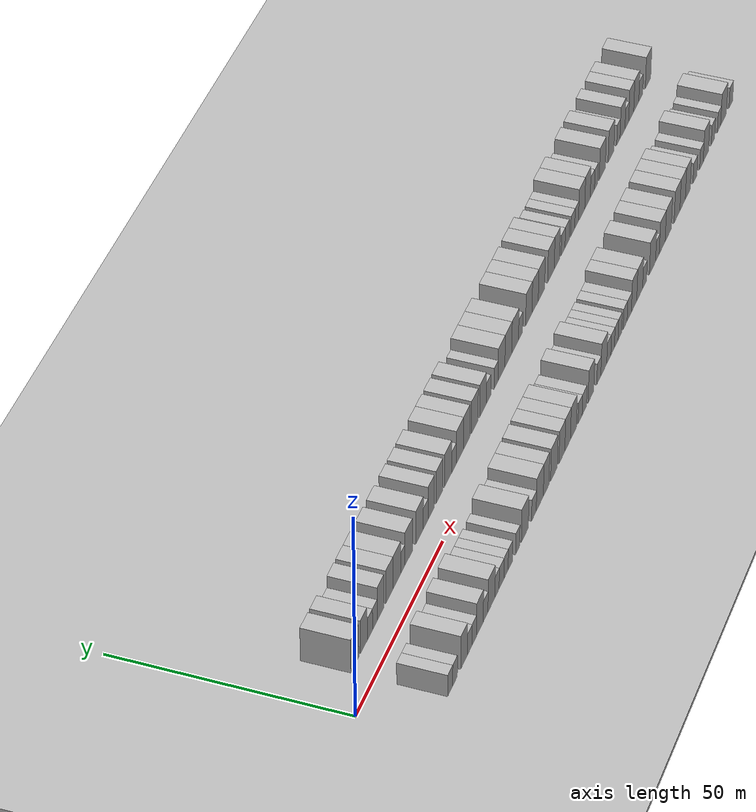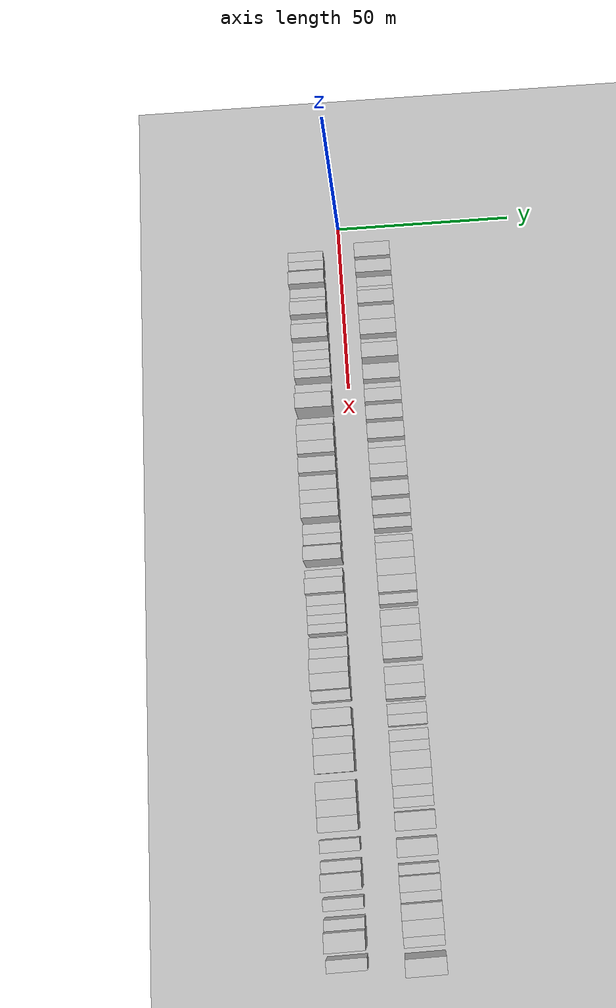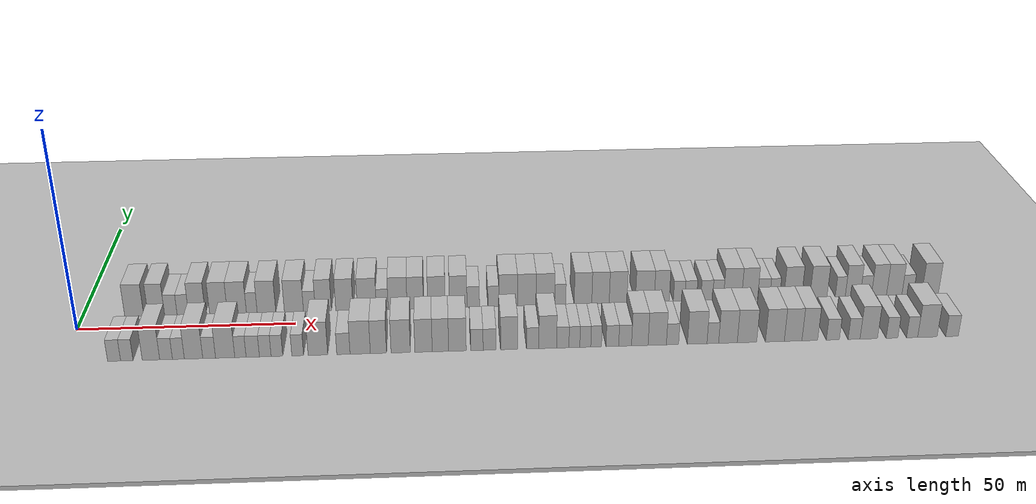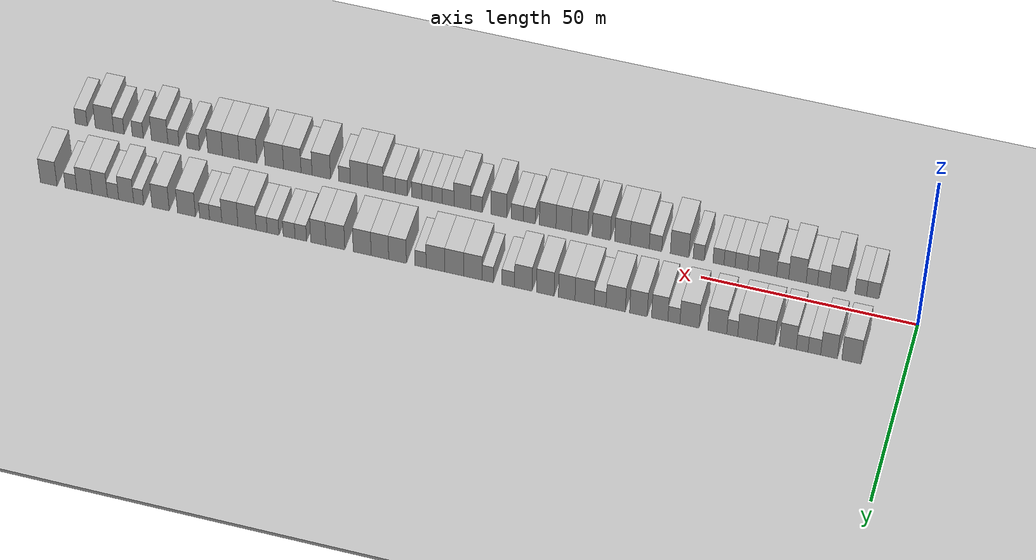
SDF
<?xml version="1.0" encoding="utf-8"?>

<sdf version="1.6">

   <world name="default">

      <gui fullscreen="0">

         <camera name="user_camera">

            <pose>-15 0 4.57585 0 0 0</pose>

            <view_controller>orbit</view_controller>

         </camera>

      </gui>

      <scene>

         <sky>

           <clouds>

             <speed>12</speed>

           </clouds>

         </sky>

         <ambient>0.4 0.4 0.4 1</ambient>

         <background>0.7 0.7 0.7 1</background>

         <shadows>1</shadows>

      </scene>

      <gravity>0 0 -9.8066</gravity>

      <magnetic_field>6e-06 2.3e-05 -4.2e-05</magnetic_field>

      <physics default="0" name="default_physics" type="ode">

         <ode>

            <solver>

               <type>quick</type>

               <iters>10</iters>

               <sor>1.0</sor>

               <use_dynamic_moi_rescaling>0</use_dynamic_moi_rescaling>

            </solver>

            <constraints>

               <cfm>0</cfm>

               <erp>0.2</erp>

               <contact_max_correcting_vel>100</contact_max_correcting_vel>

               <contact_surface_layer>0.001</contact_surface_layer>

            </constraints>

         </ode>

         <max_step_size>0.004</max_step_size>

         <real_time_factor>1</real_time_factor>

         <real_time_update_rate>250</real_time_update_rate>

      </physics>

      <light name="sun" type="directional">

         <cast_shadows>1</cast_shadows>

         <pose>0 0 10 0 0 0</pose>

         <diffuse>0.8 0.8 0.8 1</diffuse>

         <specular>0.2 0.2 0.2 1</specular>

         <attenuation>

            <range>1000</range>

            <constant>0.9</constant>

            <linear>0.01</linear>

            <quadratic>0.001</quadratic>

         </attenuation>

         <direction>-0.5 0.1 -0.9</direction>

      </light>

      <include>

         <name>ground_plane_1</name>

         <uri>model://HANNAS_ground_plane</uri>

         <pose>0 0 0  0 0 0</pose>

      </include>

      <include>

         <name>ground_plane_2</name>

         <uri>model://HANNAS_ground_plane</uri>

         <pose>100 0 0  0 0 0</pose>

      </include>

      <model name="building_1">

         <static>1</static>

         <pose frame="">12.1952 9.5000 0 0.000000 0.000000 1.570796</pose>

         <link name="link">

            <pose frame="">0 0 4.50 0 0 0</pose>

            <collision name="collision">

               <geometry>

                  <box>

                     <size>10.0000 4.3904 9.0000</size>

                  </box>

               </geometry>

               <max_contacts>10</max_contacts>

               <surface>

                  <contact>

                     <ode/>

                  </contact>

                  <bounce/>

                  <friction>

                     <torsional>

                        <ode/>

                     </torsional>

                     <ode/>

                  </friction>

               </surface>

            </collision>

            <visual name="visual">

               <cast_shadows>0</cast_shadows>

               <geometry>

                  <box>

                     <size>10.0000 4.3904 9.0000</size>

                  </box>

               </geometry>

               <material>

                  <script>

                     <uri>model://HANNAS_wall/materials/scripts</uri>

                     <uri>model://HANNAS_wall/materials/textures</uri>

                     <name>vrc/HANNAS_wall</name>

                  </script>

               </material>

            </visual>

            <self_collide>0</self_collide>

            <enable_wind>0</enable_wind>

            <kinematic>0</kinematic>

         </link>

      </model>

      <model name="building_2">

         <static>1</static>

         <pose frame="">17.2943 9.5000 0 0.000000 0.000000 1.570796</pose>

         <link name="link">

            <pose frame="">0 0 4.50 0 0 0</pose>

            <collision name="collision">

               <geometry>

                  <box>

                     <size>10.0000 3.8079 9.0000</size>

                  </box>

               </geometry>

               <max_contacts>10</max_contacts>

               <surface>

                  <contact>

                     <ode/>

                  </contact>

                  <bounce/>

                  <friction>

                     <torsional>

                        <ode/>

                     </torsional>

                     <ode/>

                  </friction>

               </surface>

            </collision>

            <visual name="visual">

               <cast_shadows>0</cast_shadows>

               <geometry>

                  <box>

                     <size>10.0000 3.8079 9.0000</size>

                  </box>

               </geometry>

               <material>

                  <script>

                     <uri>model://HANNAS_wall/materials/scripts</uri>

                     <uri>model://HANNAS_wall/materials/textures</uri>

                     <name>vrc/HANNAS_wall</name>

                  </script>

               </material>

            </visual>

            <self_collide>0</self_collide>

            <enable_wind>0</enable_wind>

            <kinematic>0</kinematic>

         </link>

      </model>

      <model name="building_3">

         <static>1</static>

         <pose frame="">20.6465 9.5000 0 0.000000 0.000000 1.570796</pose>

         <link name="link">

            <pose frame="">0 0 3.00 0 0 0</pose>

            <collision name="collision">

               <geometry>

                  <box>

                     <size>10.0000 2.8964 6.0000</size>

                  </box>

               </geometry>

               <max_contacts>10</max_contacts>

               <surface>

                  <contact>

                     <ode/>

                  </contact>

                  <bounce/>

                  <friction>

                     <torsional>

                        <ode/>

                     </torsional>

                     <ode/>

                  </friction>

               </surface>

            </collision>

            <visual name="visual">

               <cast_shadows>0</cast_shadows>

               <geometry>

                  <box>

                     <size>10.0000 2.8964 6.0000</size>

                  </box>

               </geometry>

               <material>

                  <script>

                     <uri>model://HANNAS_wall/materials/scripts</uri>

                     <uri>model://HANNAS_wall/materials/textures</uri>

                     <name>vrc/HANNAS_wall</name>

                  </script>

               </material>

            </visual>

            <self_collide>0</self_collide>

            <enable_wind>0</enable_wind>

            <kinematic>0</kinematic>

         </link>

      </model>

      <model name="building_4">

         <static>1</static>

         <pose frame="">23.4257 9.5000 0 0.000000 0.000000 1.570796</pose>

         <link name="link">

            <pose frame="">0 0 3.00 0 0 0</pose>

            <collision name="collision">

               <geometry>

                  <box>

                     <size>10.0000 2.6621 6.0000</size>

                  </box>

               </geometry>

               <max_contacts>10</max_contacts>

               <surface>

                  <contact>

                     <ode/>

                  </contact>

                  <bounce/>

                  <friction>

                     <torsional>

                        <ode/>

                     </torsional>

                     <ode/>

                  </friction>

               </surface>

            </collision>

            <visual name="visual">

               <cast_shadows>0</cast_shadows>

               <geometry>

                  <box>

                     <size>10.0000 2.6621 6.0000</size>

                  </box>

               </geometry>

               <material>

                  <script>

                     <uri>model://HANNAS_wall/materials/scripts</uri>

                     <uri>model://HANNAS_wall/materials/textures</uri>

                     <name>vrc/HANNAS_wall</name>

                  </script>

               </material>

            </visual>

            <self_collide>0</self_collide>

            <enable_wind>0</enable_wind>

            <kinematic>0</kinematic>

         </link>

      </model>

      <model name="building_5">

         <static>1</static>

         <pose frame="">26.6972 9.5000 0 0.000000 0.000000 1.570796</pose>

         <link name="link">

            <pose frame="">0 0 4.50 0 0 0</pose>

            <collision name="collision">

               <geometry>

                  <box>

                     <size>10.0000 3.8809 9.0000</size>

                  </box>

               </geometry>

               <max_contacts>10</max_contacts>

               <surface>

                  <contact>

                     <ode/>

                  </contact>

                  <bounce/>

                  <friction>

                     <torsional>

                        <ode/>

                     </torsional>

                     <ode/>

                  </friction>

               </surface>

            </collision>

            <visual name="visual">

               <cast_shadows>0</cast_shadows>

               <geometry>

                  <box>

                     <size>10.0000 3.8809 9.0000</size>

                  </box>

               </geometry>

               <material>

                  <script>

                     <uri>model://HANNAS_wall/materials/scripts</uri>

                     <uri>model://HANNAS_wall/materials/textures</uri>

                     <name>vrc/HANNAS_wall</name>

                  </script>

               </material>

            </visual>

            <self_collide>0</self_collide>

            <enable_wind>0</enable_wind>

            <kinematic>0</kinematic>

         </link>

      </model>

      <model name="building_6">

         <static>1</static>

         <pose frame="">31.6975 9.5000 0 0.000000 0.000000 1.570796</pose>

         <link name="link">

            <pose frame="">0 0 4.50 0 0 0</pose>

            <collision name="collision">

               <geometry>

                  <box>

                     <size>10.0000 4.1196 9.0000</size>

                  </box>

               </geometry>

               <max_contacts>10</max_contacts>

               <surface>

                  <contact>

                     <ode/>

                  </contact>

                  <bounce/>

                  <friction>

                     <torsional>

                        <ode/>

                     </torsional>

                     <ode/>

                  </friction>

               </surface>

            </collision>

            <visual name="visual">

               <cast_shadows>0</cast_shadows>

               <geometry>

                  <box>

                     <size>10.0000 4.1196 9.0000</size>

                  </box>

               </geometry>

               <material>

                  <script>

                     <uri>model://HANNAS_wall/materials/scripts</uri>

                     <uri>model://HANNAS_wall/materials/textures</uri>

                     <name>vrc/HANNAS_wall</name>

                  </script>

               </material>

            </visual>

            <self_collide>0</self_collide>

            <enable_wind>0</enable_wind>

            <kinematic>0</kinematic>

         </link>

      </model>

      <model name="building_7">

         <static>1</static>

         <pose frame="">35.9691 9.5000 0 0.000000 0.000000 1.570796</pose>

         <link name="link">

            <pose frame="">0 0 4.50 0 0 0</pose>

            <collision name="collision">

               <geometry>

                  <box>

                     <size>10.0000 4.4238 9.0000</size>

                  </box>

               </geometry>

               <max_contacts>10</max_contacts>

               <surface>

                  <contact>

                     <ode/>

                  </contact>

                  <bounce/>

                  <friction>

                     <torsional>

                        <ode/>

                     </torsional>

                     <ode/>

                  </friction>

               </surface>

            </collision>

            <visual name="visual">

               <cast_shadows>0</cast_shadows>

               <geometry>

                  <box>

                     <size>10.0000 4.4238 9.0000</size>

                  </box>

               </geometry>

               <material>

                  <script>

                     <uri>model://HANNAS_wall/materials/scripts</uri>

                     <uri>model://HANNAS_wall/materials/textures</uri>

                     <name>vrc/HANNAS_wall</name>

                  </script>

               </material>

            </visual>

            <self_collide>0</self_collide>

            <enable_wind>0</enable_wind>

            <kinematic>0</kinematic>

         </link>

      </model>

      <model name="building_8">

         <static>1</static>

         <pose frame="">39.4314 9.5000 0 0.000000 0.000000 1.570796</pose>

         <link name="link">

            <pose frame="">0 0 3.00 0 0 0</pose>

            <collision name="collision">

               <geometry>

                  <box>

                     <size>10.0000 2.5007 6.0000</size>

                  </box>

               </geometry>

               <max_contacts>10</max_contacts>

               <surface>

                  <contact>

                     <ode/>

                  </contact>

                  <bounce/>

                  <friction>

                     <torsional>

                        <ode/>

                     </torsional>

                     <ode/>

                  </friction>

               </surface>

            </collision>

            <visual name="visual">

               <cast_shadows>0</cast_shadows>

               <geometry>

                  <box>

                     <size>10.0000 2.5007 6.0000</size>

                  </box>

               </geometry>

               <material>

                  <script>

                     <uri>model://HANNAS_wall/materials/scripts</uri>

                     <uri>model://HANNAS_wall/materials/textures</uri>

                     <name>vrc/HANNAS_wall</name>

                  </script>

               </material>

            </visual>

            <self_collide>0</self_collide>

            <enable_wind>0</enable_wind>

            <kinematic>0</kinematic>

         </link>

      </model>

      <model name="building_9">

         <static>1</static>

         <pose frame="">42.8500 9.5000 0 0.000000 0.000000 1.570796</pose>

         <link name="link">

            <pose frame="">0 0 4.50 0 0 0</pose>

            <collision name="collision">

               <geometry>

                  <box>

                     <size>10.0000 4.3365 9.0000</size>

                  </box>

               </geometry>

               <max_contacts>10</max_contacts>

               <surface>

                  <contact>

                     <ode/>

                  </contact>

                  <bounce/>

                  <friction>

                     <torsional>

                        <ode/>

                     </torsional>

                     <ode/>

                  </friction>

               </surface>

            </collision>

            <visual name="visual">

               <cast_shadows>0</cast_shadows>

               <geometry>

                  <box>

                     <size>10.0000 4.3365 9.0000</size>

                  </box>

               </geometry>

               <material>

                  <script>

                     <uri>model://HANNAS_wall/materials/scripts</uri>

                     <uri>model://HANNAS_wall/materials/textures</uri>

                     <name>vrc/HANNAS_wall</name>

                  </script>

               </material>

            </visual>

            <self_collide>0</self_collide>

            <enable_wind>0</enable_wind>

            <kinematic>0</kinematic>

         </link>

      </model>

      <model name="building_10">

         <static>1</static>

         <pose frame="">49.2461 9.5000 0 0.000000 0.000000 1.570796</pose>

         <link name="link">

            <pose frame="">0 0 4.50 0 0 0</pose>

            <collision name="collision">

               <geometry>

                  <box>

                     <size>10.0000 4.4557 9.0000</size>

                  </box>

               </geometry>

               <max_contacts>10</max_contacts>

               <surface>

                  <contact>

                     <ode/>

                  </contact>

                  <bounce/>

                  <friction>

                     <torsional>

                        <ode/>

                     </torsional>

                     <ode/>

                  </friction>

               </surface>

            </collision>

            <visual name="visual">

               <cast_shadows>0</cast_shadows>

               <geometry>

                  <box>

                     <size>10.0000 4.4557 9.0000</size>

                  </box>

               </geometry>

               <material>

                  <script>

                     <uri>model://HANNAS_wall/materials/scripts</uri>

                     <uri>model://HANNAS_wall/materials/textures</uri>

                     <name>vrc/HANNAS_wall</name>

                  </script>

               </material>

            </visual>

            <self_collide>0</self_collide>

            <enable_wind>0</enable_wind>

            <kinematic>0</kinematic>

         </link>

      </model>

      <model name="building_11">

         <static>1</static>

         <pose frame="">52.8624 9.5000 0 0.000000 0.000000 1.570796</pose>

         <link name="link">

            <pose frame="">0 0 3.00 0 0 0</pose>

            <collision name="collision">

               <geometry>

                  <box>

                     <size>10.0000 2.7770 6.0000</size>

                  </box>

               </geometry>

               <max_contacts>10</max_contacts>

               <surface>

                  <contact>

                     <ode/>

                  </contact>

                  <bounce/>

                  <friction>

                     <torsional>

                        <ode/>

                     </torsional>

                     <ode/>

                  </friction>

               </surface>

            </collision>

            <visual name="visual">

               <cast_shadows>0</cast_shadows>

               <geometry>

                  <box>

                     <size>10.0000 2.7770 6.0000</size>

                  </box>

               </geometry>

               <material>

                  <script>

                     <uri>model://HANNAS_wall/materials/scripts</uri>

                     <uri>model://HANNAS_wall/materials/textures</uri>

                     <name>vrc/HANNAS_wall</name>

                  </script>

               </material>

            </visual>

            <self_collide>0</self_collide>

            <enable_wind>0</enable_wind>

            <kinematic>0</kinematic>

         </link>

      </model>

      <model name="building_12">

         <static>1</static>

         <pose frame="">56.1337 9.5000 0 0.000000 0.000000 1.570796</pose>

         <link name="link">

            <pose frame="">0 0 4.50 0 0 0</pose>

            <collision name="collision">

               <geometry>

                  <box>

                     <size>10.0000 3.7655 9.0000</size>

                  </box>

               </geometry>

               <max_contacts>10</max_contacts>

               <surface>

                  <contact>

                     <ode/>

                  </contact>

                  <bounce/>

                  <friction>

                     <torsional>

                        <ode/>

                     </torsional>

                     <ode/>

                  </friction>

               </surface>

            </collision>

            <visual name="visual">

               <cast_shadows>0</cast_shadows>

               <geometry>

                  <box>

                     <size>10.0000 3.7655 9.0000</size>

                  </box>

               </geometry>

               <material>

                  <script>

                     <uri>model://HANNAS_wall/materials/scripts</uri>

                     <uri>model://HANNAS_wall/materials/textures</uri>

                     <name>vrc/HANNAS_wall</name>

                  </script>

               </material>

            </visual>

            <self_collide>0</self_collide>

            <enable_wind>0</enable_wind>

            <kinematic>0</kinematic>

         </link>

      </model>

      <model name="building_13">

         <static>1</static>

         <pose frame="">61.0541 9.5000 0 0.000000 0.000000 1.570796</pose>

         <link name="link">

            <pose frame="">0 0 4.50 0 0 0</pose>

            <collision name="collision">

               <geometry>

                  <box>

                     <size>10.0000 4.0752 9.0000</size>

                  </box>

               </geometry>

               <max_contacts>10</max_contacts>

               <surface>

                  <contact>

                     <ode/>

                  </contact>

                  <bounce/>

                  <friction>

                     <torsional>

                        <ode/>

                     </torsional>

                     <ode/>

                  </friction>

               </surface>

            </collision>

            <visual name="visual">

               <cast_shadows>0</cast_shadows>

               <geometry>

                  <box>

                     <size>10.0000 4.0752 9.0000</size>

                  </box>

               </geometry>

               <material>

                  <script>

                     <uri>model://HANNAS_wall/materials/scripts</uri>

                     <uri>model://HANNAS_wall/materials/textures</uri>

                     <name>vrc/HANNAS_wall</name>

                  </script>

               </material>

            </visual>

            <self_collide>0</self_collide>

            <enable_wind>0</enable_wind>

            <kinematic>0</kinematic>

         </link>

      </model>

      <model name="building_14">

         <static>1</static>

         <pose frame="">66.3223 9.5000 0 0.000000 0.000000 1.570796</pose>

         <link name="link">

            <pose frame="">0 0 4.50 0 0 0</pose>

            <collision name="collision">

               <geometry>

                  <box>

                     <size>10.0000 4.4613 9.0000</size>

                  </box>

               </geometry>

               <max_contacts>10</max_contacts>

               <surface>

                  <contact>

                     <ode/>

                  </contact>

                  <bounce/>

                  <friction>

                     <torsional>

                        <ode/>

                     </torsional>

                     <ode/>

                  </friction>

               </surface>

            </collision>

            <visual name="visual">

               <cast_shadows>0</cast_shadows>

               <geometry>

                  <box>

                     <size>10.0000 4.4613 9.0000</size>

                  </box>

               </geometry>

               <material>

                  <script>

                     <uri>model://HANNAS_wall/materials/scripts</uri>

                     <uri>model://HANNAS_wall/materials/textures</uri>

                     <name>vrc/HANNAS_wall</name>

                  </script>

               </material>

            </visual>

            <self_collide>0</self_collide>

            <enable_wind>0</enable_wind>

            <kinematic>0</kinematic>

         </link>

      </model>

      <model name="building_15">

         <static>1</static>

         <pose frame="">69.9328 9.5000 0 0.000000 0.000000 1.570796</pose>

         <link name="link">

            <pose frame="">0 0 3.00 0 0 0</pose>

            <collision name="collision">

               <geometry>

                  <box>

                     <size>10.0000 2.7596 6.0000</size>

                  </box>

               </geometry>

               <max_contacts>10</max_contacts>

               <surface>

                  <contact>

                     <ode/>

                  </contact>

                  <bounce/>

                  <friction>

                     <torsional>

                        <ode/>

                     </torsional>

                     <ode/>

                  </friction>

               </surface>

            </collision>

            <visual name="visual">

               <cast_shadows>0</cast_shadows>

               <geometry>

                  <box>

                     <size>10.0000 2.7596 6.0000</size>

                  </box>

               </geometry>

               <material>

                  <script>

                     <uri>model://HANNAS_wall/materials/scripts</uri>

                     <uri>model://HANNAS_wall/materials/textures</uri>

                     <name>vrc/HANNAS_wall</name>

                  </script>

               </material>

            </visual>

            <self_collide>0</self_collide>

            <enable_wind>0</enable_wind>

            <kinematic>0</kinematic>

         </link>

      </model>

      <model name="building_16">

         <static>1</static>

         <pose frame="">73.5438 9.5000 0 0.000000 0.000000 1.570796</pose>

         <link name="link">

            <pose frame="">0 0 4.50 0 0 0</pose>

            <collision name="collision">

               <geometry>

                  <box>

                     <size>10.0000 4.4626 9.0000</size>

                  </box>

               </geometry>

               <max_contacts>10</max_contacts>

               <surface>

                  <contact>

                     <ode/>

                  </contact>

                  <bounce/>

                  <friction>

                     <torsional>

                        <ode/>

                     </torsional>

                     <ode/>

                  </friction>

               </surface>

            </collision>

            <visual name="visual">

               <cast_shadows>0</cast_shadows>

               <geometry>

                  <box>

                     <size>10.0000 4.4626 9.0000</size>

                  </box>

               </geometry>

               <material>

                  <script>

                     <uri>model://HANNAS_wall/materials/scripts</uri>

                     <uri>model://HANNAS_wall/materials/textures</uri>

                     <name>vrc/HANNAS_wall</name>

                  </script>

               </material>

            </visual>

            <self_collide>0</self_collide>

            <enable_wind>0</enable_wind>

            <kinematic>0</kinematic>

         </link>

      </model>

      <model name="building_17">

         <static>1</static>

         <pose frame="">77.7067 9.5000 0 0.000000 0.000000 1.570796</pose>

         <link name="link">

            <pose frame="">0 0 4.50 0 0 0</pose>

            <collision name="collision">

               <geometry>

                  <box>

                     <size>10.0000 3.8632 9.0000</size>

                  </box>

               </geometry>

               <max_contacts>10</max_contacts>

               <surface>

                  <contact>

                     <ode/>

                  </contact>

                  <bounce/>

                  <friction>

                     <torsional>

                        <ode/>

                     </torsional>

                     <ode/>

                  </friction>

               </surface>

            </collision>

            <visual name="visual">

               <cast_shadows>0</cast_shadows>

               <geometry>

                  <box>

                     <size>10.0000 3.8632 9.0000</size>

                  </box>

               </geometry>

               <material>

                  <script>

                     <uri>model://HANNAS_wall/materials/scripts</uri>

                     <uri>model://HANNAS_wall/materials/textures</uri>

                     <name>vrc/HANNAS_wall</name>

                  </script>

               </material>

            </visual>

            <self_collide>0</self_collide>

            <enable_wind>0</enable_wind>

            <kinematic>0</kinematic>

         </link>

      </model>

      <model name="building_18">

         <static>1</static>

         <pose frame="">82.6979 9.5000 0 0.000000 0.000000 1.570796</pose>

         <link name="link">

            <pose frame="">0 0 4.50 0 0 0</pose>

            <collision name="collision">

               <geometry>

                  <box>

                     <size>10.0000 4.1193 9.0000</size>

                  </box>

               </geometry>

               <max_contacts>10</max_contacts>

               <surface>

                  <contact>

                     <ode/>

                  </contact>

                  <bounce/>

                  <friction>

                     <torsional>

                        <ode/>

                     </torsional>

                     <ode/>

                  </friction>

               </surface>

            </collision>

            <visual name="visual">

               <cast_shadows>0</cast_shadows>

               <geometry>

                  <box>

                     <size>10.0000 4.1193 9.0000</size>

                  </box>

               </geometry>

               <material>

                  <script>

                     <uri>model://HANNAS_wall/materials/scripts</uri>

                     <uri>model://HANNAS_wall/materials/textures</uri>

                     <name>vrc/HANNAS_wall</name>

                  </script>

               </material>

            </visual>

            <self_collide>0</self_collide>

            <enable_wind>0</enable_wind>

            <kinematic>0</kinematic>

         </link>

      </model>

      <model name="building_19">

         <static>1</static>

         <pose frame="">87.8192 9.5000 0 0.000000 0.000000 1.570796</pose>

         <link name="link">

            <pose frame="">0 0 4.50 0 0 0</pose>

            <collision name="collision">

               <geometry>

                  <box>

                     <size>10.0000 4.1233 9.0000</size>

                  </box>

               </geometry>

               <max_contacts>10</max_contacts>

               <surface>

                  <contact>

                     <ode/>

                  </contact>

                  <bounce/>

                  <friction>

                     <torsional>

                        <ode/>

                     </torsional>

                     <ode/>

                  </friction>

               </surface>

            </collision>

            <visual name="visual">

               <cast_shadows>0</cast_shadows>

               <geometry>

                  <box>

                     <size>10.0000 4.1233 9.0000</size>

                  </box>

               </geometry>

               <material>

                  <script>

                     <uri>model://HANNAS_wall/materials/scripts</uri>

                     <uri>model://HANNAS_wall/materials/textures</uri>

                     <name>vrc/HANNAS_wall</name>

                  </script>

               </material>

            </visual>

            <self_collide>0</self_collide>

            <enable_wind>0</enable_wind>

            <kinematic>0</kinematic>

         </link>

      </model>

      <model name="building_20">

         <static>1</static>

         <pose frame="">91.3578 9.5000 0 0.000000 0.000000 1.570796</pose>

         <link name="link">

            <pose frame="">0 0 3.00 0 0 0</pose>

            <collision name="collision">

               <geometry>

                  <box>

                     <size>10.0000 2.9539 6.0000</size>

                  </box>

               </geometry>

               <max_contacts>10</max_contacts>

               <surface>

                  <contact>

                     <ode/>

                  </contact>

                  <bounce/>

                  <friction>

                     <torsional>

                        <ode/>

                     </torsional>

                     <ode/>

                  </friction>

               </surface>

            </collision>

            <visual name="visual">

               <cast_shadows>0</cast_shadows>

               <geometry>

                  <box>

                     <size>10.0000 2.9539 6.0000</size>

                  </box>

               </geometry>

               <material>

                  <script>

                     <uri>model://HANNAS_wall/materials/scripts</uri>

                     <uri>model://HANNAS_wall/materials/textures</uri>

                     <name>vrc/HANNAS_wall</name>

                  </script>

               </material>

            </visual>

            <self_collide>0</self_collide>

            <enable_wind>0</enable_wind>

            <kinematic>0</kinematic>

         </link>

      </model>

      <model name="building_21">

         <static>1</static>

         <pose frame="">96.1265 9.5000 0 0.000000 0.000000 1.570796</pose>

         <link name="link">

            <pose frame="">0 0 3.00 0 0 0</pose>

            <collision name="collision">

               <geometry>

                  <box>

                     <size>10.0000 2.5835 6.0000</size>

                  </box>

               </geometry>

               <max_contacts>10</max_contacts>

               <surface>

                  <contact>

                     <ode/>

                  </contact>

                  <bounce/>

                  <friction>

                     <torsional>

                        <ode/>

                     </torsional>

                     <ode/>

                  </friction>

               </surface>

            </collision>

            <visual name="visual">

               <cast_shadows>0</cast_shadows>

               <geometry>

                  <box>

                     <size>10.0000 2.5835 6.0000</size>

                  </box>

               </geometry>

               <material>

                  <script>

                     <uri>model://HANNAS_wall/materials/scripts</uri>

                     <uri>model://HANNAS_wall/materials/textures</uri>

                     <name>vrc/HANNAS_wall</name>

                  </script>

               </material>

            </visual>

            <self_collide>0</self_collide>

            <enable_wind>0</enable_wind>

            <kinematic>0</kinematic>

         </link>

      </model>

      <model name="building_22">

         <static>1</static>

         <pose frame="">99.6186 9.5000 0 0.000000 0.000000 1.570796</pose>

         <link name="link">

            <pose frame="">0 0 4.50 0 0 0</pose>

            <collision name="collision">

               <geometry>

                  <box>

                     <size>10.0000 4.4008 9.0000</size>

                  </box>

               </geometry>

               <max_contacts>10</max_contacts>

               <surface>

                  <contact>

                     <ode/>

                  </contact>

                  <bounce/>

                  <friction>

                     <torsional>

                        <ode/>

                     </torsional>

                     <ode/>

                  </friction>

               </surface>

            </collision>

            <visual name="visual">

               <cast_shadows>0</cast_shadows>

               <geometry>

                  <box>

                     <size>10.0000 4.4008 9.0000</size>

                  </box>

               </geometry>

               <material>

                  <script>

                     <uri>model://HANNAS_wall/materials/scripts</uri>

                     <uri>model://HANNAS_wall/materials/textures</uri>

                     <name>vrc/HANNAS_wall</name>

                  </script>

               </material>

            </visual>

            <self_collide>0</self_collide>

            <enable_wind>0</enable_wind>

            <kinematic>0</kinematic>

         </link>

      </model>

      <model name="building_23">

         <static>1</static>

         <pose frame="">104.0349 9.5000 0 0.000000 0.000000 1.570796</pose>

         <link name="link">

            <pose frame="">0 0 4.50 0 0 0</pose>

            <collision name="collision">

               <geometry>

                  <box>

                     <size>10.0000 4.4318 9.0000</size>

                  </box>

               </geometry>

               <max_contacts>10</max_contacts>

               <surface>

                  <contact>

                     <ode/>

                  </contact>

                  <bounce/>

                  <friction>

                     <torsional>

                        <ode/>

                     </torsional>

                     <ode/>

                  </friction>

               </surface>

            </collision>

            <visual name="visual">

               <cast_shadows>0</cast_shadows>

               <geometry>

                  <box>

                     <size>10.0000 4.4318 9.0000</size>

                  </box>

               </geometry>

               <material>

                  <script>

                     <uri>model://HANNAS_wall/materials/scripts</uri>

                     <uri>model://HANNAS_wall/materials/textures</uri>

                     <name>vrc/HANNAS_wall</name>

                  </script>

               </material>

            </visual>

            <self_collide>0</self_collide>

            <enable_wind>0</enable_wind>

            <kinematic>0</kinematic>

         </link>

      </model>

      <model name="building_24">

         <static>1</static>

         <pose frame="">108.4501 9.5000 0 0.000000 0.000000 1.570796</pose>

         <link name="link">

            <pose frame="">0 0 4.50 0 0 0</pose>

            <collision name="collision">

               <geometry>

                  <box>

                     <size>10.0000 4.3986 9.0000</size>

                  </box>

               </geometry>

               <max_contacts>10</max_contacts>

               <surface>

                  <contact>

                     <ode/>

                  </contact>

                  <bounce/>

                  <friction>

                     <torsional>

                        <ode/>

                     </torsional>

                     <ode/>

                  </friction>

               </surface>

            </collision>

            <visual name="visual">

               <cast_shadows>0</cast_shadows>

               <geometry>

                  <box>

                     <size>10.0000 4.3986 9.0000</size>

                  </box>

               </geometry>

               <material>

                  <script>

                     <uri>model://HANNAS_wall/materials/scripts</uri>

                     <uri>model://HANNAS_wall/materials/textures</uri>

                     <name>vrc/HANNAS_wall</name>

                  </script>

               </material>

            </visual>

            <self_collide>0</self_collide>

            <enable_wind>0</enable_wind>

            <kinematic>0</kinematic>

         </link>

      </model>

      <model name="building_25">

         <static>1</static>

         <pose frame="">111.9761 9.5000 0 0.000000 0.000000 1.570796</pose>

         <link name="link">

            <pose frame="">0 0 3.00 0 0 0</pose>

            <collision name="collision">

               <geometry>

                  <box>

                     <size>10.0000 2.6534 6.0000</size>

                  </box>

               </geometry>

               <max_contacts>10</max_contacts>

               <surface>

                  <contact>

                     <ode/>

                  </contact>

                  <bounce/>

                  <friction>

                     <torsional>

                        <ode/>

                     </torsional>

                     <ode/>

                  </friction>

               </surface>

            </collision>

            <visual name="visual">

               <cast_shadows>0</cast_shadows>

               <geometry>

                  <box>

                     <size>10.0000 2.6534 6.0000</size>

                  </box>

               </geometry>

               <material>

                  <script>

                     <uri>model://HANNAS_wall/materials/scripts</uri>

                     <uri>model://HANNAS_wall/materials/textures</uri>

                     <name>vrc/HANNAS_wall</name>

                  </script>

               </material>

            </visual>

            <self_collide>0</self_collide>

            <enable_wind>0</enable_wind>

            <kinematic>0</kinematic>

         </link>

      </model>

      <model name="building_26">

         <static>1</static>

         <pose frame="">117.3991 9.5000 0 0.000000 0.000000 1.570796</pose>

         <link name="link">

            <pose frame="">0 0 4.50 0 0 0</pose>

            <collision name="collision">

               <geometry>

                  <box>

                     <size>10.0000 4.1927 9.0000</size>

                  </box>

               </geometry>

               <max_contacts>10</max_contacts>

               <surface>

                  <contact>

                     <ode/>

                  </contact>

                  <bounce/>

                  <friction>

                     <torsional>

                        <ode/>

                     </torsional>

                     <ode/>

                  </friction>

               </surface>

            </collision>

            <visual name="visual">

               <cast_shadows>0</cast_shadows>

               <geometry>

                  <box>

                     <size>10.0000 4.1927 9.0000</size>

                  </box>

               </geometry>

               <material>

                  <script>

                     <uri>model://HANNAS_wall/materials/scripts</uri>

                     <uri>model://HANNAS_wall/materials/textures</uri>

                     <name>vrc/HANNAS_wall</name>

                  </script>

               </material>

            </visual>

            <self_collide>0</self_collide>

            <enable_wind>0</enable_wind>

            <kinematic>0</kinematic>

         </link>

      </model>

      <model name="building_27">

         <static>1</static>

         <pose frame="">121.5725 9.5000 0 0.000000 0.000000 1.570796</pose>

         <link name="link">

            <pose frame="">0 0 4.50 0 0 0</pose>

            <collision name="collision">

               <geometry>

                  <box>

                     <size>10.0000 4.1540 9.0000</size>

                  </box>

               </geometry>

               <max_contacts>10</max_contacts>

               <surface>

                  <contact>

                     <ode/>

                  </contact>

                  <bounce/>

                  <friction>

                     <torsional>

                        <ode/>

                     </torsional>

                     <ode/>

                  </friction>

               </surface>

            </collision>

            <visual name="visual">

               <cast_shadows>0</cast_shadows>

               <geometry>

                  <box>

                     <size>10.0000 4.1540 9.0000</size>

                  </box>

               </geometry>

               <material>

                  <script>

                     <uri>model://HANNAS_wall/materials/scripts</uri>

                     <uri>model://HANNAS_wall/materials/textures</uri>

                     <name>vrc/HANNAS_wall</name>

                  </script>

               </material>

            </visual>

            <self_collide>0</self_collide>

            <enable_wind>0</enable_wind>

            <kinematic>0</kinematic>

         </link>

      </model>

      <model name="building_28">

         <static>1</static>

         <pose frame="">125.7727 9.5000 0 0.000000 0.000000 1.570796</pose>

         <link name="link">

            <pose frame="">0 0 4.50 0 0 0</pose>

            <collision name="collision">

               <geometry>

                  <box>

                     <size>10.0000 4.2464 9.0000</size>

                  </box>

               </geometry>

               <max_contacts>10</max_contacts>

               <surface>

                  <contact>

                     <ode/>

                  </contact>

                  <bounce/>

                  <friction>

                     <torsional>

                        <ode/>

                     </torsional>

                     <ode/>

                  </friction>

               </surface>

            </collision>

            <visual name="visual">

               <cast_shadows>0</cast_shadows>

               <geometry>

                  <box>

                     <size>10.0000 4.2464 9.0000</size>

                  </box>

               </geometry>

               <material>

                  <script>

                     <uri>model://HANNAS_wall/materials/scripts</uri>

                     <uri>model://HANNAS_wall/materials/textures</uri>

                     <name>vrc/HANNAS_wall</name>

                  </script>

               </material>

            </visual>

            <self_collide>0</self_collide>

            <enable_wind>0</enable_wind>

            <kinematic>0</kinematic>

         </link>

      </model>

      <model name="building_29">

         <static>1</static>

         <pose frame="">132.1418 9.5000 0 0.000000 0.000000 1.570796</pose>

         <link name="link">

            <pose frame="">0 0 4.50 0 0 0</pose>

            <collision name="collision">

               <geometry>

                  <box>

                     <size>10.0000 4.4919 9.0000</size>

                  </box>

               </geometry>

               <max_contacts>10</max_contacts>

               <surface>

                  <contact>

                     <ode/>

                  </contact>

                  <bounce/>

                  <friction>

                     <torsional>

                        <ode/>

                     </torsional>

                     <ode/>

                  </friction>

               </surface>

            </collision>

            <visual name="visual">

               <cast_shadows>0</cast_shadows>

               <geometry>

                  <box>

                     <size>10.0000 4.4919 9.0000</size>

                  </box>

               </geometry>

               <material>

                  <script>

                     <uri>model://HANNAS_wall/materials/scripts</uri>

                     <uri>model://HANNAS_wall/materials/textures</uri>

                     <name>vrc/HANNAS_wall</name>

                  </script>

               </material>

            </visual>

            <self_collide>0</self_collide>

            <enable_wind>0</enable_wind>

            <kinematic>0</kinematic>

         </link>

      </model>

      <model name="building_30">

         <static>1</static>

         <pose frame="">136.1891 9.5000 0 0.000000 0.000000 1.570796</pose>

         <link name="link">

            <pose frame="">0 0 4.50 0 0 0</pose>

            <collision name="collision">

               <geometry>

                  <box>

                     <size>10.0000 3.6027 9.0000</size>

                  </box>

               </geometry>

               <max_contacts>10</max_contacts>

               <surface>

                  <contact>

                     <ode/>

                  </contact>

                  <bounce/>

                  <friction>

                     <torsional>

                        <ode/>

                     </torsional>

                     <ode/>

                  </friction>

               </surface>

            </collision>

            <visual name="visual">

               <cast_shadows>0</cast_shadows>

               <geometry>

                  <box>

                     <size>10.0000 3.6027 9.0000</size>

                  </box>

               </geometry>

               <material>

                  <script>

                     <uri>model://HANNAS_wall/materials/scripts</uri>

                     <uri>model://HANNAS_wall/materials/textures</uri>

                     <name>vrc/HANNAS_wall</name>

                  </script>

               </material>

            </visual>

            <self_collide>0</self_collide>

            <enable_wind>0</enable_wind>

            <kinematic>0</kinematic>

         </link>

      </model>

      <model name="building_31">

         <static>1</static>

         <pose frame="">140.3614 9.5000 0 0.000000 0.000000 1.570796</pose>

         <link name="link">

            <pose frame="">0 0 3.00 0 0 0</pose>

            <collision name="collision">

               <geometry>

                  <box>

                     <size>10.0000 2.7417 6.0000</size>

                  </box>

               </geometry>

               <max_contacts>10</max_contacts>

               <surface>

                  <contact>

                     <ode/>

                  </contact>

                  <bounce/>

                  <friction>

                     <torsional>

                        <ode/>

                     </torsional>

                     <ode/>

                  </friction>

               </surface>

            </collision>

            <visual name="visual">

               <cast_shadows>0</cast_shadows>

               <geometry>

                  <box>

                     <size>10.0000 2.7417 6.0000</size>

                  </box>

               </geometry>

               <material>

                  <script>

                     <uri>model://HANNAS_wall/materials/scripts</uri>

                     <uri>model://HANNAS_wall/materials/textures</uri>

                     <name>vrc/HANNAS_wall</name>

                  </script>

               </material>

            </visual>

            <self_collide>0</self_collide>

            <enable_wind>0</enable_wind>

            <kinematic>0</kinematic>

         </link>

      </model>

      <model name="building_32">

         <static>1</static>

         <pose frame="">143.1497 9.5000 0 0.000000 0.000000 1.570796</pose>

         <link name="link">

            <pose frame="">0 0 3.00 0 0 0</pose>

            <collision name="collision">

               <geometry>

                  <box>

                     <size>10.0000 2.8349 6.0000</size>

                  </box>

               </geometry>

               <max_contacts>10</max_contacts>

               <surface>

                  <contact>

                     <ode/>

                  </contact>

                  <bounce/>

                  <friction>

                     <torsional>

                        <ode/>

                     </torsional>

                     <ode/>

                  </friction>

               </surface>

            </collision>

            <visual name="visual">

               <cast_shadows>0</cast_shadows>

               <geometry>

                  <box>

                     <size>10.0000 2.8349 6.0000</size>

                  </box>

               </geometry>

               <material>

                  <script>

                     <uri>model://HANNAS_wall/materials/scripts</uri>

                     <uri>model://HANNAS_wall/materials/textures</uri>

                     <name>vrc/HANNAS_wall</name>

                  </script>

               </material>

            </visual>

            <self_collide>0</self_collide>

            <enable_wind>0</enable_wind>

            <kinematic>0</kinematic>

         </link>

      </model>

      <model name="building_33">

         <static>1</static>

         <pose frame="">146.9822 9.5000 0 0.000000 0.000000 1.570796</pose>

         <link name="link">

            <pose frame="">0 0 3.00 0 0 0</pose>

            <collision name="collision">

               <geometry>

                  <box>

                     <size>10.0000 2.8301 6.0000</size>

                  </box>

               </geometry>

               <max_contacts>10</max_contacts>

               <surface>

                  <contact>

                     <ode/>

                  </contact>

                  <bounce/>

                  <friction>

                     <torsional>

                        <ode/>

                     </torsional>

                     <ode/>

                  </friction>

               </surface>

            </collision>

            <visual name="visual">

               <cast_shadows>0</cast_shadows>

               <geometry>

                  <box>

                     <size>10.0000 2.8301 6.0000</size>

                  </box>

               </geometry>

               <material>

                  <script>

                     <uri>model://HANNAS_wall/materials/scripts</uri>

                     <uri>model://HANNAS_wall/materials/textures</uri>

                     <name>vrc/HANNAS_wall</name>

                  </script>

               </material>

            </visual>

            <self_collide>0</self_collide>

            <enable_wind>0</enable_wind>

            <kinematic>0</kinematic>

         </link>

      </model>

      <model name="building_34">

         <static>1</static>

         <pose frame="">149.7100 9.5000 0 0.000000 0.000000 1.570796</pose>

         <link name="link">

            <pose frame="">0 0 3.00 0 0 0</pose>

            <collision name="collision">

               <geometry>

                  <box>

                     <size>10.0000 2.6255 6.0000</size>

                  </box>

               </geometry>

               <max_contacts>10</max_contacts>

               <surface>

                  <contact>

                     <ode/>

                  </contact>

                  <bounce/>

                  <friction>

                     <torsional>

                        <ode/>

                     </torsional>

                     <ode/>

                  </friction>

               </surface>

            </collision>

            <visual name="visual">

               <cast_shadows>0</cast_shadows>

               <geometry>

                  <box>

                     <size>10.0000 2.6255 6.0000</size>

                  </box>

               </geometry>

               <material>

                  <script>

                     <uri>model://HANNAS_wall/materials/scripts</uri>

                     <uri>model://HANNAS_wall/materials/textures</uri>

                     <name>vrc/HANNAS_wall</name>

                  </script>

               </material>

            </visual>

            <self_collide>0</self_collide>

            <enable_wind>0</enable_wind>

            <kinematic>0</kinematic>

         </link>

      </model>

      <model name="building_35">

         <static>1</static>

         <pose frame="">153.2073 9.5000 0 0.000000 0.000000 1.570796</pose>

         <link name="link">

            <pose frame="">0 0 4.50 0 0 0</pose>

            <collision name="collision">

               <geometry>

                  <box>

                     <size>10.0000 4.3690 9.0000</size>

                  </box>

               </geometry>

               <max_contacts>10</max_contacts>

               <surface>

                  <contact>

                     <ode/>

                  </contact>

                  <bounce/>

                  <friction>

                     <torsional>

                        <ode/>

                     </torsional>

                     <ode/>

                  </friction>

               </surface>

            </collision>

            <visual name="visual">

               <cast_shadows>0</cast_shadows>

               <geometry>

                  <box>

                     <size>10.0000 4.3690 9.0000</size>

                  </box>

               </geometry>

               <material>

                  <script>

                     <uri>model://HANNAS_wall/materials/scripts</uri>

                     <uri>model://HANNAS_wall/materials/textures</uri>

                     <name>vrc/HANNAS_wall</name>

                  </script>

               </material>

            </visual>

            <self_collide>0</self_collide>

            <enable_wind>0</enable_wind>

            <kinematic>0</kinematic>

         </link>

      </model>

      <model name="building_36">

         <static>1</static>

         <pose frame="">157.3263 9.5000 0 0.000000 0.000000 1.570796</pose>

         <link name="link">

            <pose frame="">0 0 4.50 0 0 0</pose>

            <collision name="collision">

               <geometry>

                  <box>

                     <size>10.0000 3.8691 9.0000</size>

                  </box>

               </geometry>

               <max_contacts>10</max_contacts>

               <surface>

                  <contact>

                     <ode/>

                  </contact>

                  <bounce/>

                  <friction>

                     <torsional>

                        <ode/>

                     </torsional>

                     <ode/>

                  </friction>

               </surface>

            </collision>

            <visual name="visual">

               <cast_shadows>0</cast_shadows>

               <geometry>

                  <box>

                     <size>10.0000 3.8691 9.0000</size>

                  </box>

               </geometry>

               <material>

                  <script>

                     <uri>model://HANNAS_wall/materials/scripts</uri>

                     <uri>model://HANNAS_wall/materials/textures</uri>

                     <name>vrc/HANNAS_wall</name>

                  </script>

               </material>

            </visual>

            <self_collide>0</self_collide>

            <enable_wind>0</enable_wind>

            <kinematic>0</kinematic>

         </link>

      </model>

      <model name="building_37">

         <static>1</static>

         <pose frame="">160.7287 9.5000 0 0.000000 0.000000 1.570796</pose>

         <link name="link">

            <pose frame="">0 0 3.00 0 0 0</pose>

            <collision name="collision">

               <geometry>

                  <box>

                     <size>10.0000 2.9357 6.0000</size>

                  </box>

               </geometry>

               <max_contacts>10</max_contacts>

               <surface>

                  <contact>

                     <ode/>

                  </contact>

                  <bounce/>

                  <friction>

                     <torsional>

                        <ode/>

                     </torsional>

                     <ode/>

                  </friction>

               </surface>

            </collision>

            <visual name="visual">

               <cast_shadows>0</cast_shadows>

               <geometry>

                  <box>

                     <size>10.0000 2.9357 6.0000</size>

                  </box>

               </geometry>

               <material>

                  <script>

                     <uri>model://HANNAS_wall/materials/scripts</uri>

                     <uri>model://HANNAS_wall/materials/textures</uri>

                     <name>vrc/HANNAS_wall</name>

                  </script>

               </material>

            </visual>

            <self_collide>0</self_collide>

            <enable_wind>0</enable_wind>

            <kinematic>0</kinematic>

         </link>

      </model>

      <model name="building_38">

         <static>1</static>

         <pose frame="">163.3969 9.5000 0 0.000000 0.000000 1.570796</pose>

         <link name="link">

            <pose frame="">0 0 3.00 0 0 0</pose>

            <collision name="collision">

               <geometry>

                  <box>

                     <size>10.0000 2.4005 6.0000</size>

                  </box>

               </geometry>

               <max_contacts>10</max_contacts>

               <surface>

                  <contact>

                     <ode/>

                  </contact>

                  <bounce/>

                  <friction>

                     <torsional>

                        <ode/>

                     </torsional>

                     <ode/>

                  </friction>

               </surface>

            </collision>

            <visual name="visual">

               <cast_shadows>0</cast_shadows>

               <geometry>

                  <box>

                     <size>10.0000 2.4005 6.0000</size>

                  </box>

               </geometry>

               <material>

                  <script>

                     <uri>model://HANNAS_wall/materials/scripts</uri>

                     <uri>model://HANNAS_wall/materials/textures</uri>

                     <name>vrc/HANNAS_wall</name>

                  </script>

               </material>

            </visual>

            <self_collide>0</self_collide>

            <enable_wind>0</enable_wind>

            <kinematic>0</kinematic>

         </link>

      </model>

      <model name="building_39">

         <static>1</static>

         <pose frame="">167.7573 9.5000 0 0.000000 0.000000 1.570796</pose>

         <link name="link">

            <pose frame="">0 0 4.50 0 0 0</pose>

            <collision name="collision">

               <geometry>

                  <box>

                     <size>10.0000 4.3204 9.0000</size>

                  </box>

               </geometry>

               <max_contacts>10</max_contacts>

               <surface>

                  <contact>

                     <ode/>

                  </contact>

                  <bounce/>

                  <friction>

                     <torsional>

                        <ode/>

                     </torsional>

                     <ode/>

                  </friction>

               </surface>

            </collision>

            <visual name="visual">

               <cast_shadows>0</cast_shadows>

               <geometry>

                  <box>

                     <size>10.0000 4.3204 9.0000</size>

                  </box>

               </geometry>

               <material>

                  <script>

                     <uri>model://HANNAS_wall/materials/scripts</uri>

                     <uri>model://HANNAS_wall/materials/textures</uri>

                     <name>vrc/HANNAS_wall</name>

                  </script>

               </material>

            </visual>

            <self_collide>0</self_collide>

            <enable_wind>0</enable_wind>

            <kinematic>0</kinematic>

         </link>

      </model>

      <model name="building_40">

         <static>1</static>

         <pose frame="">173.9975 9.5000 0 0.000000 0.000000 1.570796</pose>

         <link name="link">

            <pose frame="">0 0 4.50 0 0 0</pose>

            <collision name="collision">

               <geometry>

                  <box>

                     <size>10.0000 4.1599 9.0000</size>

                  </box>

               </geometry>

               <max_contacts>10</max_contacts>

               <surface>

                  <contact>

                     <ode/>

                  </contact>

                  <bounce/>

                  <friction>

                     <torsional>

                        <ode/>

                     </torsional>

                     <ode/>

                  </friction>

               </surface>

            </collision>

            <visual name="visual">

               <cast_shadows>0</cast_shadows>

               <geometry>

                  <box>

                     <size>10.0000 4.1599 9.0000</size>

                  </box>

               </geometry>

               <material>

                  <script>

                     <uri>model://HANNAS_wall/materials/scripts</uri>

                     <uri>model://HANNAS_wall/materials/textures</uri>

                     <name>vrc/HANNAS_wall</name>

                  </script>

               </material>

            </visual>

            <self_collide>0</self_collide>

            <enable_wind>0</enable_wind>

            <kinematic>0</kinematic>

         </link>

      </model>

      <model name="building_41">

         <static>1</static>

         <pose frame="">179.2896 9.5000 0 0.000000 0.000000 1.570796</pose>

         <link name="link">

            <pose frame="">0 0 3.00 0 0 0</pose>

            <collision name="collision">

               <geometry>

                  <box>

                     <size>10.0000 2.4242 6.0000</size>

                  </box>

               </geometry>

               <max_contacts>10</max_contacts>

               <surface>

                  <contact>

                     <ode/>

                  </contact>

                  <bounce/>

                  <friction>

                     <torsional>

                        <ode/>

                     </torsional>

                     <ode/>

                  </friction>

               </surface>

            </collision>

            <visual name="visual">

               <cast_shadows>0</cast_shadows>

               <geometry>

                  <box>

                     <size>10.0000 2.4242 6.0000</size>

                  </box>

               </geometry>

               <material>

                  <script>

                     <uri>model://HANNAS_wall/materials/scripts</uri>

                     <uri>model://HANNAS_wall/materials/textures</uri>

                     <name>vrc/HANNAS_wall</name>

                  </script>

               </material>

            </visual>

            <self_collide>0</self_collide>

            <enable_wind>0</enable_wind>

            <kinematic>0</kinematic>

         </link>

      </model>

      <model name="building_42">

         <static>1</static>

         <pose frame="">182.3201 9.5000 0 0.000000 0.000000 1.570796</pose>

         <link name="link">

            <pose frame="">0 0 4.50 0 0 0</pose>

            <collision name="collision">

               <geometry>

                  <box>

                     <size>10.0000 3.6369 9.0000</size>

                  </box>

               </geometry>

               <max_contacts>10</max_contacts>

               <surface>

                  <contact>

                     <ode/>

                  </contact>

                  <bounce/>

                  <friction>

                     <torsional>

                        <ode/>

                     </torsional>

                     <ode/>

                  </friction>

               </surface>

            </collision>

            <visual name="visual">

               <cast_shadows>0</cast_shadows>

               <geometry>

                  <box>

                     <size>10.0000 3.6369 9.0000</size>

                  </box>

               </geometry>

               <material>

                  <script>

                     <uri>model://HANNAS_wall/materials/scripts</uri>

                     <uri>model://HANNAS_wall/materials/textures</uri>

                     <name>vrc/HANNAS_wall</name>

                  </script>

               </material>

            </visual>

            <self_collide>0</self_collide>

            <enable_wind>0</enable_wind>

            <kinematic>0</kinematic>

         </link>

      </model>

      <model name="building_43">

         <static>1</static>

         <pose frame="">185.5018 9.5000 0 0.000000 0.000000 1.570796</pose>

         <link name="link">

            <pose frame="">0 0 3.00 0 0 0</pose>

            <collision name="collision">

               <geometry>

                  <box>

                     <size>10.0000 2.7267 6.0000</size>

                  </box>

               </geometry>

               <max_contacts>10</max_contacts>

               <surface>

                  <contact>

                     <ode/>

                  </contact>

                  <bounce/>

                  <friction>

                     <torsional>

                        <ode/>

                     </torsional>

                     <ode/>

                  </friction>

               </surface>

            </collision>

            <visual name="visual">

               <cast_shadows>0</cast_shadows>

               <geometry>

                  <box>

                     <size>10.0000 2.7267 6.0000</size>

                  </box>

               </geometry>

               <material>

                  <script>

                     <uri>model://HANNAS_wall/materials/scripts</uri>

                     <uri>model://HANNAS_wall/materials/textures</uri>

                     <name>vrc/HANNAS_wall</name>

                  </script>

               </material>

            </visual>

            <self_collide>0</self_collide>

            <enable_wind>0</enable_wind>

            <kinematic>0</kinematic>

         </link>

      </model>

      <model name="building_44">

         <static>1</static>

         <pose frame="">188.6957 9.5000 0 0.000000 0.000000 1.570796</pose>

         <link name="link">

            <pose frame="">0 0 4.50 0 0 0</pose>

            <collision name="collision">

               <geometry>

                  <box>

                     <size>10.0000 3.6610 9.0000</size>

                  </box>

               </geometry>

               <max_contacts>10</max_contacts>

               <surface>

                  <contact>

                     <ode/>

                  </contact>

                  <bounce/>

                  <friction>

                     <torsional>

                        <ode/>

                     </torsional>

                     <ode/>

                  </friction>

               </surface>

            </collision>

            <visual name="visual">

               <cast_shadows>0</cast_shadows>

               <geometry>

                  <box>

                     <size>10.0000 3.6610 9.0000</size>

                  </box>

               </geometry>

               <material>

                  <script>

                     <uri>model://HANNAS_wall/materials/scripts</uri>

                     <uri>model://HANNAS_wall/materials/textures</uri>

                     <name>vrc/HANNAS_wall</name>

                  </script>

               </material>

            </visual>

            <self_collide>0</self_collide>

            <enable_wind>0</enable_wind>

            <kinematic>0</kinematic>

         </link>

      </model>

      <model name="building_45">

         <static>1</static>

         <pose frame="">192.4081 9.5000 0 0.000000 0.000000 1.570796</pose>

         <link name="link">

            <pose frame="">0 0 4.50 0 0 0</pose>

            <collision name="collision">

               <geometry>

                  <box>

                     <size>10.0000 3.7639 9.0000</size>

                  </box>

               </geometry>

               <max_contacts>10</max_contacts>

               <surface>

                  <contact>

                     <ode/>

                  </contact>

                  <bounce/>

                  <friction>

                     <torsional>

                        <ode/>

                     </torsional>

                     <ode/>

                  </friction>

               </surface>

            </collision>

            <visual name="visual">

               <cast_shadows>0</cast_shadows>

               <geometry>

                  <box>

                     <size>10.0000 3.7639 9.0000</size>

                  </box>

               </geometry>

               <material>

                  <script>

                     <uri>model://HANNAS_wall/materials/scripts</uri>

                     <uri>model://HANNAS_wall/materials/textures</uri>

                     <name>vrc/HANNAS_wall</name>

                  </script>

               </material>

            </visual>

            <self_collide>0</self_collide>

            <enable_wind>0</enable_wind>

            <kinematic>0</kinematic>

         </link>

      </model>

      <model name="building_46">

         <static>1</static>

         <pose frame="">195.7033 9.5000 0 0.000000 0.000000 1.570796</pose>

         <link name="link">

            <pose frame="">0 0 3.00 0 0 0</pose>

            <collision name="collision">

               <geometry>

                  <box>

                     <size>10.0000 2.8263 6.0000</size>

                  </box>

               </geometry>

               <max_contacts>10</max_contacts>

               <surface>

                  <contact>

                     <ode/>

                  </contact>

                  <bounce/>

                  <friction>

                     <torsional>

                        <ode/>

                     </torsional>

                     <ode/>

                  </friction>

               </surface>

            </collision>

            <visual name="visual">

               <cast_shadows>0</cast_shadows>

               <geometry>

                  <box>

                     <size>10.0000 2.8263 6.0000</size>

                  </box>

               </geometry>

               <material>

                  <script>

                     <uri>model://HANNAS_wall/materials/scripts</uri>

                     <uri>model://HANNAS_wall/materials/textures</uri>

                     <name>vrc/HANNAS_wall</name>

                  </script>

               </material>

            </visual>

            <self_collide>0</self_collide>

            <enable_wind>0</enable_wind>

            <kinematic>0</kinematic>

         </link>

      </model>

      <model name="building_47">

         <static>1</static>

         <pose frame="">201.1507 9.5000 0 0.000000 0.000000 1.570796</pose>

         <link name="link">

            <pose frame="">0 0 4.50 0 0 0</pose>

            <collision name="collision">

               <geometry>

                  <box>

                     <size>10.0000 4.0687 9.0000</size>

                  </box>

               </geometry>

               <max_contacts>10</max_contacts>

               <surface>

                  <contact>

                     <ode/>

                  </contact>

                  <bounce/>

                  <friction>

                     <torsional>

                        <ode/>

                     </torsional>

                     <ode/>

                  </friction>

               </surface>

            </collision>

            <visual name="visual">

               <cast_shadows>0</cast_shadows>

               <geometry>

                  <box>

                     <size>10.0000 4.0687 9.0000</size>

                  </box>

               </geometry>

               <material>

                  <script>

                     <uri>model://HANNAS_wall/materials/scripts</uri>

                     <uri>model://HANNAS_wall/materials/textures</uri>

                     <name>vrc/HANNAS_wall</name>

                  </script>

               </material>

            </visual>

            <self_collide>0</self_collide>

            <enable_wind>0</enable_wind>

            <kinematic>0</kinematic>

         </link>

      </model>

      <model name="building_48">

         <static>1</static>

         <pose frame="">11.4273 -9.5000 0 0.000000 0.000000 1.570796</pose>

         <link name="link">

            <pose frame="">0 0 3.00 0 0 0</pose>

            <collision name="collision">

               <geometry>

                  <box>

                     <size>10.0000 2.8546 6.0000</size>

                  </box>

               </geometry>

               <max_contacts>10</max_contacts>

               <surface>

                  <contact>

                     <ode/>

                  </contact>

                  <bounce/>

                  <friction>

                     <torsional>

                        <ode/>

                     </torsional>

                     <ode/>

                  </friction>

               </surface>

            </collision>

            <visual name="visual">

               <cast_shadows>0</cast_shadows>

               <geometry>

                  <box>

                     <size>10.0000 2.8546 6.0000</size>

                  </box>

               </geometry>

               <material>

                  <script>

                     <uri>model://HANNAS_wall/materials/scripts</uri>

                     <uri>model://HANNAS_wall/materials/textures</uri>

                     <name>vrc/HANNAS_wall</name>

                  </script>

               </material>

            </visual>

            <self_collide>0</self_collide>

            <enable_wind>0</enable_wind>

            <kinematic>0</kinematic>

         </link>

      </model>

      <model name="building_49">

         <static>1</static>

         <pose frame="">14.2122 -9.5000 0 0.000000 0.000000 1.570796</pose>

         <link name="link">

            <pose frame="">0 0 3.00 0 0 0</pose>

            <collision name="collision">

               <geometry>

                  <box>

                     <size>10.0000 2.7153 6.0000</size>

                  </box>

               </geometry>

               <max_contacts>10</max_contacts>

               <surface>

                  <contact>

                     <ode/>

                  </contact>

                  <bounce/>

                  <friction>

                     <torsional>

                        <ode/>

                     </torsional>

                     <ode/>

                  </friction>

               </surface>

            </collision>

            <visual name="visual">

               <cast_shadows>0</cast_shadows>

               <geometry>

                  <box>

                     <size>10.0000 2.7153 6.0000</size>

                  </box>

               </geometry>

               <material>

                  <script>

                     <uri>model://HANNAS_wall/materials/scripts</uri>

                     <uri>model://HANNAS_wall/materials/textures</uri>

                     <name>vrc/HANNAS_wall</name>

                  </script>

               </material>

            </visual>

            <self_collide>0</self_collide>

            <enable_wind>0</enable_wind>

            <kinematic>0</kinematic>

         </link>

      </model>

      <model name="building_50">

         <static>1</static>

         <pose frame="">19.4815 -9.5000 0 0.000000 0.000000 1.570796</pose>

         <link name="link">

            <pose frame="">0 0 4.50 0 0 0</pose>

            <collision name="collision">

               <geometry>

                  <box>

                     <size>10.0000 3.8231 9.0000</size>

                  </box>

               </geometry>

               <max_contacts>10</max_contacts>

               <surface>

                  <contact>

                     <ode/>

                  </contact>

                  <bounce/>

                  <friction>

                     <torsional>

                        <ode/>

                     </torsional>

                     <ode/>

                  </friction>

               </surface>

            </collision>

            <visual name="visual">

               <cast_shadows>0</cast_shadows>

               <geometry>

                  <box>

                     <size>10.0000 3.8231 9.0000</size>

                  </box>

               </geometry>

               <material>

                  <script>

                     <uri>model://HANNAS_wall/materials/scripts</uri>

                     <uri>model://HANNAS_wall/materials/textures</uri>

                     <name>vrc/HANNAS_wall</name>

                  </script>

               </material>

            </visual>

            <self_collide>0</self_collide>

            <enable_wind>0</enable_wind>

            <kinematic>0</kinematic>

         </link>

      </model>

      <model name="building_51">

         <static>1</static>

         <pose frame="">22.7909 -9.5000 0 0.000000 0.000000 1.570796</pose>

         <link name="link">

            <pose frame="">0 0 3.00 0 0 0</pose>

            <collision name="collision">

               <geometry>

                  <box>

                     <size>10.0000 2.7958 6.0000</size>

                  </box>

               </geometry>

               <max_contacts>10</max_contacts>

               <surface>

                  <contact>

                     <ode/>

                  </contact>

                  <bounce/>

                  <friction>

                     <torsional>

                        <ode/>

                     </torsional>

                     <ode/>

                  </friction>

               </surface>

            </collision>

            <visual name="visual">

               <cast_shadows>0</cast_shadows>

               <geometry>

                  <box>

                     <size>10.0000 2.7958 6.0000</size>

                  </box>

               </geometry>

               <material>

                  <script>

                     <uri>model://HANNAS_wall/materials/scripts</uri>

                     <uri>model://HANNAS_wall/materials/textures</uri>

                     <name>vrc/HANNAS_wall</name>

                  </script>

               </material>

            </visual>

            <self_collide>0</self_collide>

            <enable_wind>0</enable_wind>

            <kinematic>0</kinematic>

         </link>

      </model>

      <model name="building_52">

         <static>1</static>

         <pose frame="">25.4921 -9.5000 0 0.000000 0.000000 1.570796</pose>

         <link name="link">

            <pose frame="">0 0 3.00 0 0 0</pose>

            <collision name="collision">

               <geometry>

                  <box>

                     <size>10.0000 2.6066 6.0000</size>

                  </box>

               </geometry>

               <max_contacts>10</max_contacts>

               <surface>

                  <contact>

                     <ode/>

                  </contact>

                  <bounce/>

                  <friction>

                     <torsional>

                        <ode/>

                     </torsional>

                     <ode/>

                  </friction>

               </surface>

            </collision>

            <visual name="visual">

               <cast_shadows>0</cast_shadows>

               <geometry>

                  <box>

                     <size>10.0000 2.6066 6.0000</size>

                  </box>

               </geometry>

               <material>

                  <script>

                     <uri>model://HANNAS_wall/materials/scripts</uri>

                     <uri>model://HANNAS_wall/materials/textures</uri>

                     <name>vrc/HANNAS_wall</name>

                  </script>

               </material>

            </visual>

            <self_collide>0</self_collide>

            <enable_wind>0</enable_wind>

            <kinematic>0</kinematic>

         </link>

      </model>

      <model name="building_53">

         <static>1</static>

         <pose frame="">28.8129 -9.5000 0 0.000000 0.000000 1.570796</pose>

         <link name="link">

            <pose frame="">0 0 4.50 0 0 0</pose>

            <collision name="collision">

               <geometry>

                  <box>

                     <size>10.0000 4.0350 9.0000</size>

                  </box>

               </geometry>

               <max_contacts>10</max_contacts>

               <surface>

                  <contact>

                     <ode/>

                  </contact>

                  <bounce/>

                  <friction>

                     <torsional>

                        <ode/>

                     </torsional>

                     <ode/>

                  </friction>

               </surface>

            </collision>

            <visual name="visual">

               <cast_shadows>0</cast_shadows>

               <geometry>

                  <box>

                     <size>10.0000 4.0350 9.0000</size>

                  </box>

               </geometry>

               <material>

                  <script>

                     <uri>model://HANNAS_wall/materials/scripts</uri>

                     <uri>model://HANNAS_wall/materials/textures</uri>

                     <name>vrc/HANNAS_wall</name>

                  </script>

               </material>

            </visual>

            <self_collide>0</self_collide>

            <enable_wind>0</enable_wind>

            <kinematic>0</kinematic>

         </link>

      </model>

      <model name="building_54">

         <static>1</static>

         <pose frame="">32.2364 -9.5000 0 0.000000 0.000000 1.570796</pose>

         <link name="link">

            <pose frame="">0 0 3.00 0 0 0</pose>

            <collision name="collision">

               <geometry>

                  <box>

                     <size>10.0000 2.8119 6.0000</size>

                  </box>

               </geometry>

               <max_contacts>10</max_contacts>

               <surface>

                  <contact>

                     <ode/>

                  </contact>

                  <bounce/>

                  <friction>

                     <torsional>

                        <ode/>

                     </torsional>

                     <ode/>

                  </friction>

               </surface>

            </collision>

            <visual name="visual">

               <cast_shadows>0</cast_shadows>

               <geometry>

                  <box>

                     <size>10.0000 2.8119 6.0000</size>

                  </box>

               </geometry>

               <material>

                  <script>

                     <uri>model://HANNAS_wall/materials/scripts</uri>

                     <uri>model://HANNAS_wall/materials/textures</uri>

                     <name>vrc/HANNAS_wall</name>

                  </script>

               </material>

            </visual>

            <self_collide>0</self_collide>

            <enable_wind>0</enable_wind>

            <kinematic>0</kinematic>

         </link>

      </model>

      <model name="building_55">

         <static>1</static>

         <pose frame="">35.7567 -9.5000 0 0.000000 0.000000 1.570796</pose>

         <link name="link">

            <pose frame="">0 0 4.50 0 0 0</pose>

            <collision name="collision">

               <geometry>

                  <box>

                     <size>10.0000 4.2289 9.0000</size>

                  </box>

               </geometry>

               <max_contacts>10</max_contacts>

               <surface>

                  <contact>

                     <ode/>

                  </contact>

                  <bounce/>

                  <friction>

                     <torsional>

                        <ode/>

                     </torsional>

                     <ode/>

                  </friction>

               </surface>

            </collision>

            <visual name="visual">

               <cast_shadows>0</cast_shadows>

               <geometry>

                  <box>

                     <size>10.0000 4.2289 9.0000</size>

                  </box>

               </geometry>

               <material>

                  <script>

                     <uri>model://HANNAS_wall/materials/scripts</uri>

                     <uri>model://HANNAS_wall/materials/textures</uri>

                     <name>vrc/HANNAS_wall</name>

                  </script>

               </material>

            </visual>

            <self_collide>0</self_collide>

            <enable_wind>0</enable_wind>

            <kinematic>0</kinematic>

         </link>

      </model>

      <model name="building_56">

         <static>1</static>

         <pose frame="">39.1147 -9.5000 0 0.000000 0.000000 1.570796</pose>

         <link name="link">

            <pose frame="">0 0 3.00 0 0 0</pose>

            <collision name="collision">

               <geometry>

                  <box>

                     <size>10.0000 2.4870 6.0000</size>

                  </box>

               </geometry>

               <max_contacts>10</max_contacts>

               <surface>

                  <contact>

                     <ode/>

                  </contact>

                  <bounce/>

                  <friction>

                     <torsional>

                        <ode/>

                     </torsional>

                     <ode/>

                  </friction>

               </surface>

            </collision>

            <visual name="visual">

               <cast_shadows>0</cast_shadows>

               <geometry>

                  <box>

                     <size>10.0000 2.4870 6.0000</size>

                  </box>

               </geometry>

               <material>

                  <script>

                     <uri>model://HANNAS_wall/materials/scripts</uri>

                     <uri>model://HANNAS_wall/materials/textures</uri>

                     <name>vrc/HANNAS_wall</name>

                  </script>

               </material>

            </visual>

            <self_collide>0</self_collide>

            <enable_wind>0</enable_wind>

            <kinematic>0</kinematic>

         </link>

      </model>

      <model name="building_57">

         <static>1</static>

         <pose frame="">41.8252 -9.5000 0 0.000000 0.000000 1.570796</pose>

         <link name="link">

            <pose frame="">0 0 3.00 0 0 0</pose>

            <collision name="collision">

               <geometry>

                  <box>

                     <size>10.0000 2.9340 6.0000</size>

                  </box>

               </geometry>

               <max_contacts>10</max_contacts>

               <surface>

                  <contact>

                     <ode/>

                  </contact>

                  <bounce/>

                  <friction>

                     <torsional>

                        <ode/>

                     </torsional>

                     <ode/>

                  </friction>

               </surface>

            </collision>

            <visual name="visual">

               <cast_shadows>0</cast_shadows>

               <geometry>

                  <box>

                     <size>10.0000 2.9340 6.0000</size>

                  </box>

               </geometry>

               <material>

                  <script>

                     <uri>model://HANNAS_wall/materials/scripts</uri>

                     <uri>model://HANNAS_wall/materials/textures</uri>

                     <name>vrc/HANNAS_wall</name>

                  </script>

               </material>

            </visual>

            <self_collide>0</self_collide>

            <enable_wind>0</enable_wind>

            <kinematic>0</kinematic>

         </link>

      </model>

      <model name="building_58">

         <static>1</static>

         <pose frame="">44.5836 -9.5000 0 0.000000 0.000000 1.570796</pose>

         <link name="link">

            <pose frame="">0 0 3.00 0 0 0</pose>

            <collision name="collision">

               <geometry>

                  <box>

                     <size>10.0000 2.5829 6.0000</size>

                  </box>

               </geometry>

               <max_contacts>10</max_contacts>

               <surface>

                  <contact>

                     <ode/>

                  </contact>

                  <bounce/>

                  <friction>

                     <torsional>

                        <ode/>

                     </torsional>

                     <ode/>

                  </friction>

               </surface>

            </collision>

            <visual name="visual">

               <cast_shadows>0</cast_shadows>

               <geometry>

                  <box>

                     <size>10.0000 2.5829 6.0000</size>

                  </box>

               </geometry>

               <material>

                  <script>

                     <uri>model://HANNAS_wall/materials/scripts</uri>

                     <uri>model://HANNAS_wall/materials/textures</uri>

                     <name>vrc/HANNAS_wall</name>

                  </script>

               </material>

            </visual>

            <self_collide>0</self_collide>

            <enable_wind>0</enable_wind>

            <kinematic>0</kinematic>

         </link>

      </model>

      <model name="building_59">

         <static>1</static>

         <pose frame="">47.1597 -9.5000 0 0.000000 0.000000 1.570796</pose>

         <link name="link">

            <pose frame="">0 0 3.00 0 0 0</pose>

            <collision name="collision">

               <geometry>

                  <box>

                     <size>10.0000 2.5693 6.0000</size>

                  </box>

               </geometry>

               <max_contacts>10</max_contacts>

               <surface>

                  <contact>

                     <ode/>

                  </contact>

                  <bounce/>

                  <friction>

                     <torsional>

                        <ode/>

                     </torsional>

                     <ode/>

                  </friction>

               </surface>

            </collision>

            <visual name="visual">

               <cast_shadows>0</cast_shadows>

               <geometry>

                  <box>

                     <size>10.0000 2.5693 6.0000</size>

                  </box>

               </geometry>

               <material>

                  <script>

                     <uri>model://HANNAS_wall/materials/scripts</uri>

                     <uri>model://HANNAS_wall/materials/textures</uri>

                     <name>vrc/HANNAS_wall</name>

                  </script>

               </material>

            </visual>

            <self_collide>0</self_collide>

            <enable_wind>0</enable_wind>

            <kinematic>0</kinematic>

         </link>

      </model>

      <model name="building_60">

         <static>1</static>

         <pose frame="">51.7449 -9.5000 0 0.000000 0.000000 1.570796</pose>

         <link name="link">

            <pose frame="">0 0 3.00 0 0 0</pose>

            <collision name="collision">

               <geometry>

                  <box>

                     <size>10.0000 2.6011 6.0000</size>

                  </box>

               </geometry>

               <max_contacts>10</max_contacts>

               <surface>

                  <contact>

                     <ode/>

                  </contact>

                  <bounce/>

                  <friction>

                     <torsional>

                        <ode/>

                     </torsional>

                     <ode/>

                  </friction>

               </surface>

            </collision>

            <visual name="visual">

               <cast_shadows>0</cast_shadows>

               <geometry>

                  <box>

                     <size>10.0000 2.6011 6.0000</size>

                  </box>

               </geometry>

               <material>

                  <script>

                     <uri>model://HANNAS_wall/materials/scripts</uri>

                     <uri>model://HANNAS_wall/materials/textures</uri>

                     <name>vrc/HANNAS_wall</name>

                  </script>

               </material>

            </visual>

            <self_collide>0</self_collide>

            <enable_wind>0</enable_wind>

            <kinematic>0</kinematic>

         </link>

      </model>

      <model name="building_61">

         <static>1</static>

         <pose frame="">56.2164 -9.5000 0 0.000000 0.000000 1.570796</pose>

         <link name="link">

            <pose frame="">0 0 4.50 0 0 0</pose>

            <collision name="collision">

               <geometry>

                  <box>

                     <size>10.0000 4.3420 9.0000</size>

                  </box>

               </geometry>

               <max_contacts>10</max_contacts>

               <surface>

                  <contact>

                     <ode/>

                  </contact>

                  <bounce/>

                  <friction>

                     <torsional>

                        <ode/>

                     </torsional>

                     <ode/>

                  </friction>

               </surface>

            </collision>

            <visual name="visual">

               <cast_shadows>0</cast_shadows>

               <geometry>

                  <box>

                     <size>10.0000 4.3420 9.0000</size>

                  </box>

               </geometry>

               <material>

                  <script>

                     <uri>model://HANNAS_wall/materials/scripts</uri>

                     <uri>model://HANNAS_wall/materials/textures</uri>

                     <name>vrc/HANNAS_wall</name>

                  </script>

               </material>

            </visual>

            <self_collide>0</self_collide>

            <enable_wind>0</enable_wind>

            <kinematic>0</kinematic>

         </link>

      </model>

      <model name="building_62">

         <static>1</static>

         <pose frame="">61.8629 -9.5000 0 0.000000 0.000000 1.570796</pose>

         <link name="link">

            <pose frame="">0 0 3.00 0 0 0</pose>

            <collision name="collision">

               <geometry>

                  <box>

                     <size>10.0000 2.9510 6.0000</size>

                  </box>

               </geometry>

               <max_contacts>10</max_contacts>

               <surface>

                  <contact>

                     <ode/>

                  </contact>

                  <bounce/>

                  <friction>

                     <torsional>

                        <ode/>

                     </torsional>

                     <ode/>

                  </friction>

               </surface>

            </collision>

            <visual name="visual">

               <cast_shadows>0</cast_shadows>

               <geometry>

                  <box>

                     <size>10.0000 2.9510 6.0000</size>

                  </box>

               </geometry>

               <material>

                  <script>

                     <uri>model://HANNAS_wall/materials/scripts</uri>

                     <uri>model://HANNAS_wall/materials/textures</uri>

                     <name>vrc/HANNAS_wall</name>

                  </script>

               </material>

            </visual>

            <self_collide>0</self_collide>

            <enable_wind>0</enable_wind>

            <kinematic>0</kinematic>

         </link>

      </model>

      <model name="building_63">

         <static>1</static>

         <pose frame="">65.5865 -9.5000 0 0.000000 0.000000 1.570796</pose>

         <link name="link">

            <pose frame="">0 0 4.50 0 0 0</pose>

            <collision name="collision">

               <geometry>

                  <box>

                     <size>10.0000 4.4961 9.0000</size>

                  </box>

               </geometry>

               <max_contacts>10</max_contacts>

               <surface>

                  <contact>

                     <ode/>

                  </contact>

                  <bounce/>

                  <friction>

                     <torsional>

                        <ode/>

                     </torsional>

                     <ode/>

                  </friction>

               </surface>

            </collision>

            <visual name="visual">

               <cast_shadows>0</cast_shadows>

               <geometry>

                  <box>

                     <size>10.0000 4.4961 9.0000</size>

                  </box>

               </geometry>

               <material>

                  <script>

                     <uri>model://HANNAS_wall/materials/scripts</uri>

                     <uri>model://HANNAS_wall/materials/textures</uri>

                     <name>vrc/HANNAS_wall</name>

                  </script>

               </material>

            </visual>

            <self_collide>0</self_collide>

            <enable_wind>0</enable_wind>

            <kinematic>0</kinematic>

         </link>

      </model>

      <model name="building_64">

         <static>1</static>

         <pose frame="">69.6377 -9.5000 0 0.000000 0.000000 1.570796</pose>

         <link name="link">

            <pose frame="">0 0 4.50 0 0 0</pose>

            <collision name="collision">

               <geometry>

                  <box>

                     <size>10.0000 3.6064 9.0000</size>

                  </box>

               </geometry>

               <max_contacts>10</max_contacts>

               <surface>

                  <contact>

                     <ode/>

                  </contact>

                  <bounce/>

                  <friction>

                     <torsional>

                        <ode/>

                     </torsional>

                     <ode/>

                  </friction>

               </surface>

            </collision>

            <visual name="visual">

               <cast_shadows>0</cast_shadows>

               <geometry>

                  <box>

                     <size>10.0000 3.6064 9.0000</size>

                  </box>

               </geometry>

               <material>

                  <script>

                     <uri>model://HANNAS_wall/materials/scripts</uri>

                     <uri>model://HANNAS_wall/materials/textures</uri>

                     <name>vrc/HANNAS_wall</name>

                  </script>

               </material>

            </visual>

            <self_collide>0</self_collide>

            <enable_wind>0</enable_wind>

            <kinematic>0</kinematic>

         </link>

      </model>

      <model name="building_65">

         <static>1</static>

         <pose frame="">74.5949 -9.5000 0 0.000000 0.000000 1.570796</pose>

         <link name="link">

            <pose frame="">0 0 4.50 0 0 0</pose>

            <collision name="collision">

               <geometry>

                  <box>

                     <size>10.0000 4.3079 9.0000</size>

                  </box>

               </geometry>

               <max_contacts>10</max_contacts>

               <surface>

                  <contact>

                     <ode/>

                  </contact>

                  <bounce/>

                  <friction>

                     <torsional>

                        <ode/>

                     </torsional>

                     <ode/>

                  </friction>

               </surface>

            </collision>

            <visual name="visual">

               <cast_shadows>0</cast_shadows>

               <geometry>

                  <box>

                     <size>10.0000 4.3079 9.0000</size>

                  </box>

               </geometry>

               <material>

                  <script>

                     <uri>model://HANNAS_wall/materials/scripts</uri>

                     <uri>model://HANNAS_wall/materials/textures</uri>

                     <name>vrc/HANNAS_wall</name>

                  </script>

               </material>

            </visual>

            <self_collide>0</self_collide>

            <enable_wind>0</enable_wind>

            <kinematic>0</kinematic>

         </link>

      </model>

      <model name="building_66">

         <static>1</static>

         <pose frame="">79.6844 -9.5000 0 0.000000 0.000000 1.570796</pose>

         <link name="link">

            <pose frame="">0 0 4.50 0 0 0</pose>

            <collision name="collision">

               <geometry>

                  <box>

                     <size>10.0000 3.8711 9.0000</size>

                  </box>

               </geometry>

               <max_contacts>10</max_contacts>

               <surface>

                  <contact>

                     <ode/>

                  </contact>

                  <bounce/>

                  <friction>

                     <torsional>

                        <ode/>

                     </torsional>

                     <ode/>

                  </friction>

               </surface>

            </collision>

            <visual name="visual">

               <cast_shadows>0</cast_shadows>

               <geometry>

                  <box>

                     <size>10.0000 3.8711 9.0000</size>

                  </box>

               </geometry>

               <material>

                  <script>

                     <uri>model://HANNAS_wall/materials/scripts</uri>

                     <uri>model://HANNAS_wall/materials/textures</uri>

                     <name>vrc/HANNAS_wall</name>

                  </script>

               </material>

            </visual>

            <self_collide>0</self_collide>

            <enable_wind>0</enable_wind>

            <kinematic>0</kinematic>

         </link>

      </model>

      <model name="building_67">

         <static>1</static>

         <pose frame="">83.4515 -9.5000 0 0.000000 0.000000 1.570796</pose>

         <link name="link">

            <pose frame="">0 0 4.50 0 0 0</pose>

            <collision name="collision">

               <geometry>

                  <box>

                     <size>10.0000 3.6631 9.0000</size>

                  </box>

               </geometry>

               <max_contacts>10</max_contacts>

               <surface>

                  <contact>

                     <ode/>

                  </contact>

                  <bounce/>

                  <friction>

                     <torsional>

                        <ode/>

                     </torsional>

                     <ode/>

                  </friction>

               </surface>

            </collision>

            <visual name="visual">

               <cast_shadows>0</cast_shadows>

               <geometry>

                  <box>

                     <size>10.0000 3.6631 9.0000</size>

                  </box>

               </geometry>

               <material>

                  <script>

                     <uri>model://HANNAS_wall/materials/scripts</uri>

                     <uri>model://HANNAS_wall/materials/textures</uri>

                     <name>vrc/HANNAS_wall</name>

                  </script>

               </material>

            </visual>

            <self_collide>0</self_collide>

            <enable_wind>0</enable_wind>

            <kinematic>0</kinematic>

         </link>

      </model>

      <model name="building_68">

         <static>1</static>

         <pose frame="">87.2488 -9.5000 0 0.000000 0.000000 1.570796</pose>

         <link name="link">

            <pose frame="">0 0 4.50 0 0 0</pose>

            <collision name="collision">

               <geometry>

                  <box>

                     <size>10.0000 3.9315 9.0000</size>

                  </box>

               </geometry>

               <max_contacts>10</max_contacts>

               <surface>

                  <contact>

                     <ode/>

                  </contact>

                  <bounce/>

                  <friction>

                     <torsional>

                        <ode/>

                     </torsional>

                     <ode/>

                  </friction>

               </surface>

            </collision>

            <visual name="visual">

               <cast_shadows>0</cast_shadows>

               <geometry>

                  <box>

                     <size>10.0000 3.9315 9.0000</size>

                  </box>

               </geometry>

               <material>

                  <script>

                     <uri>model://HANNAS_wall/materials/scripts</uri>

                     <uri>model://HANNAS_wall/materials/textures</uri>

                     <name>vrc/HANNAS_wall</name>

                  </script>

               </material>

            </visual>

            <self_collide>0</self_collide>

            <enable_wind>0</enable_wind>

            <kinematic>0</kinematic>

         </link>

      </model>

      <model name="building_69">

         <static>1</static>

         <pose frame="">91.6026 -9.5000 0 0.000000 0.000000 1.570796</pose>

         <link name="link">

            <pose frame="">0 0 3.00 0 0 0</pose>

            <collision name="collision">

               <geometry>

                  <box>

                     <size>10.0000 2.7761 6.0000</size>

                  </box>

               </geometry>

               <max_contacts>10</max_contacts>

               <surface>

                  <contact>

                     <ode/>

                  </contact>

                  <bounce/>

                  <friction>

                     <torsional>

                        <ode/>

                     </torsional>

                     <ode/>

                  </friction>

               </surface>

            </collision>

            <visual name="visual">

               <cast_shadows>0</cast_shadows>

               <geometry>

                  <box>

                     <size>10.0000 2.7761 6.0000</size>

                  </box>

               </geometry>

               <material>

                  <script>

                     <uri>model://HANNAS_wall/materials/scripts</uri>

                     <uri>model://HANNAS_wall/materials/textures</uri>

                     <name>vrc/HANNAS_wall</name>

                  </script>

               </material>

            </visual>

            <self_collide>0</self_collide>

            <enable_wind>0</enable_wind>

            <kinematic>0</kinematic>

         </link>

      </model>

      <model name="building_70">

         <static>1</static>

         <pose frame="">94.4490 -9.5000 0 0.000000 0.000000 1.570796</pose>

         <link name="link">

            <pose frame="">0 0 3.00 0 0 0</pose>

            <collision name="collision">

               <geometry>

                  <box>

                     <size>10.0000 2.9165 6.0000</size>

                  </box>

               </geometry>

               <max_contacts>10</max_contacts>

               <surface>

                  <contact>

                     <ode/>

                  </contact>

                  <bounce/>

                  <friction>

                     <torsional>

                        <ode/>

                     </torsional>

                     <ode/>

                  </friction>

               </surface>

            </collision>

            <visual name="visual">

               <cast_shadows>0</cast_shadows>

               <geometry>

                  <box>

                     <size>10.0000 2.9165 6.0000</size>

                  </box>

               </geometry>

               <material>

                  <script>

                     <uri>model://HANNAS_wall/materials/scripts</uri>

                     <uri>model://HANNAS_wall/materials/textures</uri>

                     <name>vrc/HANNAS_wall</name>

                  </script>

               </material>

            </visual>

            <self_collide>0</self_collide>

            <enable_wind>0</enable_wind>

            <kinematic>0</kinematic>

         </link>

      </model>

      <model name="building_71">

         <static>1</static>

         <pose frame="">98.8161 -9.5000 0 0.000000 0.000000 1.570796</pose>

         <link name="link">

            <pose frame="">0 0 4.50 0 0 0</pose>

            <collision name="collision">

               <geometry>

                  <box>

                     <size>10.0000 3.8177 9.0000</size>

                  </box>

               </geometry>

               <max_contacts>10</max_contacts>

               <surface>

                  <contact>

                     <ode/>

                  </contact>

                  <bounce/>

                  <friction>

                     <torsional>

                        <ode/>

                     </torsional>

                     <ode/>

                  </friction>

               </surface>

            </collision>

            <visual name="visual">

               <cast_shadows>0</cast_shadows>

               <geometry>

                  <box>

                     <size>10.0000 3.8177 9.0000</size>

                  </box>

               </geometry>

               <material>

                  <script>

                     <uri>model://HANNAS_wall/materials/scripts</uri>

                     <uri>model://HANNAS_wall/materials/textures</uri>

                     <name>vrc/HANNAS_wall</name>

                  </script>

               </material>

            </visual>

            <self_collide>0</self_collide>

            <enable_wind>0</enable_wind>

            <kinematic>0</kinematic>

         </link>

      </model>

      <model name="building_72">

         <static>1</static>

         <pose frame="">104.1056 -9.5000 0 0.000000 0.000000 1.570796</pose>

         <link name="link">

            <pose frame="">0 0 3.00 0 0 0</pose>

            <collision name="collision">

               <geometry>

                  <box>

                     <size>10.0000 2.7614 6.0000</size>

                  </box>

               </geometry>

               <max_contacts>10</max_contacts>

               <surface>

                  <contact>

                     <ode/>

                  </contact>

                  <bounce/>

                  <friction>

                     <torsional>

                        <ode/>

                     </torsional>

                     <ode/>

                  </friction>

               </surface>

            </collision>

            <visual name="visual">

               <cast_shadows>0</cast_shadows>

               <geometry>

                  <box>

                     <size>10.0000 2.7614 6.0000</size>

                  </box>

               </geometry>

               <material>

                  <script>

                     <uri>model://HANNAS_wall/materials/scripts</uri>

                     <uri>model://HANNAS_wall/materials/textures</uri>

                     <name>vrc/HANNAS_wall</name>

                  </script>

               </material>

            </visual>

            <self_collide>0</self_collide>

            <enable_wind>0</enable_wind>

            <kinematic>0</kinematic>

         </link>

      </model>

      <model name="building_73">

         <static>1</static>

         <pose frame="">107.4928 -9.5000 0 0.000000 0.000000 1.570796</pose>

         <link name="link">

            <pose frame="">0 0 4.50 0 0 0</pose>

            <collision name="collision">

               <geometry>

                  <box>

                     <size>10.0000 4.0130 9.0000</size>

                  </box>

               </geometry>

               <max_contacts>10</max_contacts>

               <surface>

                  <contact>

                     <ode/>

                  </contact>

                  <bounce/>

                  <friction>

                     <torsional>

                        <ode/>

                     </torsional>

                     <ode/>

                  </friction>

               </surface>

            </collision>

            <visual name="visual">

               <cast_shadows>0</cast_shadows>

               <geometry>

                  <box>

                     <size>10.0000 4.0130 9.0000</size>

                  </box>

               </geometry>

               <material>

                  <script>

                     <uri>model://HANNAS_wall/materials/scripts</uri>

                     <uri>model://HANNAS_wall/materials/textures</uri>

                     <name>vrc/HANNAS_wall</name>

                  </script>

               </material>

            </visual>

            <self_collide>0</self_collide>

            <enable_wind>0</enable_wind>

            <kinematic>0</kinematic>

         </link>

      </model>

      <model name="building_74">

         <static>1</static>

         <pose frame="">110.8842 -9.5000 0 0.000000 0.000000 1.570796</pose>

         <link name="link">

            <pose frame="">0 0 3.00 0 0 0</pose>

            <collision name="collision">

               <geometry>

                  <box>

                     <size>10.0000 2.7699 6.0000</size>

                  </box>

               </geometry>

               <max_contacts>10</max_contacts>

               <surface>

                  <contact>

                     <ode/>

                  </contact>

                  <bounce/>

                  <friction>

                     <torsional>

                        <ode/>

                     </torsional>

                     <ode/>

                  </friction>

               </surface>

            </collision>

            <visual name="visual">

               <cast_shadows>0</cast_shadows>

               <geometry>

                  <box>

                     <size>10.0000 2.7699 6.0000</size>

                  </box>

               </geometry>

               <material>

                  <script>

                     <uri>model://HANNAS_wall/materials/scripts</uri>

                     <uri>model://HANNAS_wall/materials/textures</uri>

                     <name>vrc/HANNAS_wall</name>

                  </script>

               </material>

            </visual>

            <self_collide>0</self_collide>

            <enable_wind>0</enable_wind>

            <kinematic>0</kinematic>

         </link>

      </model>

      <model name="building_75">

         <static>1</static>

         <pose frame="">113.4985 -9.5000 0 0.000000 0.000000 1.570796</pose>

         <link name="link">

            <pose frame="">0 0 3.00 0 0 0</pose>

            <collision name="collision">

               <geometry>

                  <box>

                     <size>10.0000 2.4585 6.0000</size>

                  </box>

               </geometry>

               <max_contacts>10</max_contacts>

               <surface>

                  <contact>

                     <ode/>

                  </contact>

                  <bounce/>

                  <friction>

                     <torsional>

                        <ode/>

                     </torsional>

                     <ode/>

                  </friction>

               </surface>

            </collision>

            <visual name="visual">

               <cast_shadows>0</cast_shadows>

               <geometry>

                  <box>

                     <size>10.0000 2.4585 6.0000</size>

                  </box>

               </geometry>

               <material>

                  <script>

                     <uri>model://HANNAS_wall/materials/scripts</uri>

                     <uri>model://HANNAS_wall/materials/textures</uri>

                     <name>vrc/HANNAS_wall</name>

                  </script>

               </material>

            </visual>

            <self_collide>0</self_collide>

            <enable_wind>0</enable_wind>

            <kinematic>0</kinematic>

         </link>

      </model>

      <model name="building_76">

         <static>1</static>

         <pose frame="">115.9655 -9.5000 0 0.000000 0.000000 1.570796</pose>

         <link name="link">

            <pose frame="">0 0 3.00 0 0 0</pose>

            <collision name="collision">

               <geometry>

                  <box>

                     <size>10.0000 2.4755 6.0000</size>

                  </box>

               </geometry>

               <max_contacts>10</max_contacts>

               <surface>

                  <contact>

                     <ode/>

                  </contact>

                  <bounce/>

                  <friction>

                     <torsional>

                        <ode/>

                     </torsional>

                     <ode/>

                  </friction>

               </surface>

            </collision>

            <visual name="visual">

               <cast_shadows>0</cast_shadows>

               <geometry>

                  <box>

                     <size>10.0000 2.4755 6.0000</size>

                  </box>

               </geometry>

               <material>

                  <script>

                     <uri>model://HANNAS_wall/materials/scripts</uri>

                     <uri>model://HANNAS_wall/materials/textures</uri>

                     <name>vrc/HANNAS_wall</name>

                  </script>

               </material>

            </visual>

            <self_collide>0</self_collide>

            <enable_wind>0</enable_wind>

            <kinematic>0</kinematic>

         </link>

      </model>

      <model name="building_77">

         <static>1</static>

         <pose frame="">118.4129 -9.5000 0 0.000000 0.000000 1.570796</pose>

         <link name="link">

            <pose frame="">0 0 3.00 0 0 0</pose>

            <collision name="collision">

               <geometry>

                  <box>

                     <size>10.0000 2.4194 6.0000</size>

                  </box>

               </geometry>

               <max_contacts>10</max_contacts>

               <surface>

                  <contact>

                     <ode/>

                  </contact>

                  <bounce/>

                  <friction>

                     <torsional>

                        <ode/>

                     </torsional>

                     <ode/>

                  </friction>

               </surface>

            </collision>

            <visual name="visual">

               <cast_shadows>0</cast_shadows>

               <geometry>

                  <box>

                     <size>10.0000 2.4194 6.0000</size>

                  </box>

               </geometry>

               <material>

                  <script>

                     <uri>model://HANNAS_wall/materials/scripts</uri>

                     <uri>model://HANNAS_wall/materials/textures</uri>

                     <name>vrc/HANNAS_wall</name>

                  </script>

               </material>

            </visual>

            <self_collide>0</self_collide>

            <enable_wind>0</enable_wind>

            <kinematic>0</kinematic>

         </link>

      </model>

      <model name="building_78">

         <static>1</static>

         <pose frame="">122.0638 -9.5000 0 0.000000 0.000000 1.570796</pose>

         <link name="link">

            <pose frame="">0 0 3.00 0 0 0</pose>

            <collision name="collision">

               <geometry>

                  <box>

                     <size>10.0000 2.8823 6.0000</size>

                  </box>

               </geometry>

               <max_contacts>10</max_contacts>

               <surface>

                  <contact>

                     <ode/>

                  </contact>

                  <bounce/>

                  <friction>

                     <torsional>

                        <ode/>

                     </torsional>

                     <ode/>

                  </friction>

               </surface>

            </collision>

            <visual name="visual">

               <cast_shadows>0</cast_shadows>

               <geometry>

                  <box>

                     <size>10.0000 2.8823 6.0000</size>

                  </box>

               </geometry>

               <material>

                  <script>

                     <uri>model://HANNAS_wall/materials/scripts</uri>

                     <uri>model://HANNAS_wall/materials/textures</uri>

                     <name>vrc/HANNAS_wall</name>

                  </script>

               </material>

            </visual>

            <self_collide>0</self_collide>

            <enable_wind>0</enable_wind>

            <kinematic>0</kinematic>

         </link>

      </model>

      <model name="building_79">

         <static>1</static>

         <pose frame="">124.9561 -9.5000 0 0.000000 0.000000 1.570796</pose>

         <link name="link">

            <pose frame="">0 0 3.00 0 0 0</pose>

            <collision name="collision">

               <geometry>

                  <box>

                     <size>10.0000 2.9024 6.0000</size>

                  </box>

               </geometry>

               <max_contacts>10</max_contacts>

               <surface>

                  <contact>

                     <ode/>

                  </contact>

                  <bounce/>

                  <friction>

                     <torsional>

                        <ode/>

                     </torsional>

                     <ode/>

                  </friction>

               </surface>

            </collision>

            <visual name="visual">

               <cast_shadows>0</cast_shadows>

               <geometry>

                  <box>

                     <size>10.0000 2.9024 6.0000</size>

                  </box>

               </geometry>

               <material>

                  <script>

                     <uri>model://HANNAS_wall/materials/scripts</uri>

                     <uri>model://HANNAS_wall/materials/textures</uri>

                     <name>vrc/HANNAS_wall</name>

                  </script>

               </material>

            </visual>

            <self_collide>0</self_collide>

            <enable_wind>0</enable_wind>

            <kinematic>0</kinematic>

         </link>

      </model>

      <model name="building_80">

         <static>1</static>

         <pose frame="">128.2796 -9.5000 0 0.000000 0.000000 1.570796</pose>

         <link name="link">

            <pose frame="">0 0 4.50 0 0 0</pose>

            <collision name="collision">

               <geometry>

                  <box>

                     <size>10.0000 3.7445 9.0000</size>

                  </box>

               </geometry>

               <max_contacts>10</max_contacts>

               <surface>

                  <contact>

                     <ode/>

                  </contact>

                  <bounce/>

                  <friction>

                     <torsional>

                        <ode/>

                     </torsional>

                     <ode/>

                  </friction>

               </surface>

            </collision>

            <visual name="visual">

               <cast_shadows>0</cast_shadows>

               <geometry>

                  <box>

                     <size>10.0000 3.7445 9.0000</size>

                  </box>

               </geometry>

               <material>

                  <script>

                     <uri>model://HANNAS_wall/materials/scripts</uri>

                     <uri>model://HANNAS_wall/materials/textures</uri>

                     <name>vrc/HANNAS_wall</name>

                  </script>

               </material>

            </visual>

            <self_collide>0</self_collide>

            <enable_wind>0</enable_wind>

            <kinematic>0</kinematic>

         </link>

      </model>

      <model name="building_81">

         <static>1</static>

         <pose frame="">132.2312 -9.5000 0 0.000000 0.000000 1.570796</pose>

         <link name="link">

            <pose frame="">0 0 4.50 0 0 0</pose>

            <collision name="collision">

               <geometry>

                  <box>

                     <size>10.0000 4.1588 9.0000</size>

                  </box>

               </geometry>

               <max_contacts>10</max_contacts>

               <surface>

                  <contact>

                     <ode/>

                  </contact>

                  <bounce/>

                  <friction>

                     <torsional>

                        <ode/>

                     </torsional>

                     <ode/>

                  </friction>

               </surface>

            </collision>

            <visual name="visual">

               <cast_shadows>0</cast_shadows>

               <geometry>

                  <box>

                     <size>10.0000 4.1588 9.0000</size>

                  </box>

               </geometry>

               <material>

                  <script>

                     <uri>model://HANNAS_wall/materials/scripts</uri>

                     <uri>model://HANNAS_wall/materials/textures</uri>

                     <name>vrc/HANNAS_wall</name>

                  </script>

               </material>

            </visual>

            <self_collide>0</self_collide>

            <enable_wind>0</enable_wind>

            <kinematic>0</kinematic>

         </link>

      </model>

      <model name="building_82">

         <static>1</static>

         <pose frame="">135.7006 -9.5000 0 0.000000 0.000000 1.570796</pose>

         <link name="link">

            <pose frame="">0 0 3.00 0 0 0</pose>

            <collision name="collision">

               <geometry>

                  <box>

                     <size>10.0000 2.7801 6.0000</size>

                  </box>

               </geometry>

               <max_contacts>10</max_contacts>

               <surface>

                  <contact>

                     <ode/>

                  </contact>

                  <bounce/>

                  <friction>

                     <torsional>

                        <ode/>

                     </torsional>

                     <ode/>

                  </friction>

               </surface>

            </collision>

            <visual name="visual">

               <cast_shadows>0</cast_shadows>

               <geometry>

                  <box>

                     <size>10.0000 2.7801 6.0000</size>

                  </box>

               </geometry>

               <material>

                  <script>

                     <uri>model://HANNAS_wall/materials/scripts</uri>

                     <uri>model://HANNAS_wall/materials/textures</uri>

                     <name>vrc/HANNAS_wall</name>

                  </script>

               </material>

            </visual>

            <self_collide>0</self_collide>

            <enable_wind>0</enable_wind>

            <kinematic>0</kinematic>

         </link>

      </model>

      <model name="building_83">

         <static>1</static>

         <pose frame="">141.3119 -9.5000 0 0.000000 0.000000 1.570796</pose>

         <link name="link">

            <pose frame="">0 0 4.50 0 0 0</pose>

            <collision name="collision">

               <geometry>

                  <box>

                     <size>10.0000 4.4426 9.0000</size>

                  </box>

               </geometry>

               <max_contacts>10</max_contacts>

               <surface>

                  <contact>

                     <ode/>

                  </contact>

                  <bounce/>

                  <friction>

                     <torsional>

                        <ode/>

                     </torsional>

                     <ode/>

                  </friction>

               </surface>

            </collision>

            <visual name="visual">

               <cast_shadows>0</cast_shadows>

               <geometry>

                  <box>

                     <size>10.0000 4.4426 9.0000</size>

                  </box>

               </geometry>

               <material>

                  <script>

                     <uri>model://HANNAS_wall/materials/scripts</uri>

                     <uri>model://HANNAS_wall/materials/textures</uri>

                     <name>vrc/HANNAS_wall</name>

                  </script>

               </material>

            </visual>

            <self_collide>0</self_collide>

            <enable_wind>0</enable_wind>

            <kinematic>0</kinematic>

         </link>

      </model>

      <model name="building_84">

         <static>1</static>

         <pose frame="">144.8622 -9.5000 0 0.000000 0.000000 1.570796</pose>

         <link name="link">

            <pose frame="">0 0 3.00 0 0 0</pose>

            <collision name="collision">

               <geometry>

                  <box>

                     <size>10.0000 2.6580 6.0000</size>

                  </box>

               </geometry>

               <max_contacts>10</max_contacts>

               <surface>

                  <contact>

                     <ode/>

                  </contact>

                  <bounce/>

                  <friction>

                     <torsional>

                        <ode/>

                     </torsional>

                     <ode/>

                  </friction>

               </surface>

            </collision>

            <visual name="visual">

               <cast_shadows>0</cast_shadows>

               <geometry>

                  <box>

                     <size>10.0000 2.6580 6.0000</size>

                  </box>

               </geometry>

               <material>

                  <script>

                     <uri>model://HANNAS_wall/materials/scripts</uri>

                     <uri>model://HANNAS_wall/materials/textures</uri>

                     <name>vrc/HANNAS_wall</name>

                  </script>

               </material>

            </visual>

            <self_collide>0</self_collide>

            <enable_wind>0</enable_wind>

            <kinematic>0</kinematic>

         </link>

      </model>

      <model name="building_85">

         <static>1</static>

         <pose frame="">148.3122 -9.5000 0 0.000000 0.000000 1.570796</pose>

         <link name="link">

            <pose frame="">0 0 4.50 0 0 0</pose>

            <collision name="collision">

               <geometry>

                  <box>

                     <size>10.0000 4.2419 9.0000</size>

                  </box>

               </geometry>

               <max_contacts>10</max_contacts>

               <surface>

                  <contact>

                     <ode/>

                  </contact>

                  <bounce/>

                  <friction>

                     <torsional>

                        <ode/>

                     </torsional>

                     <ode/>

                  </friction>

               </surface>

            </collision>

            <visual name="visual">

               <cast_shadows>0</cast_shadows>

               <geometry>

                  <box>

                     <size>10.0000 4.2419 9.0000</size>

                  </box>

               </geometry>

               <material>

                  <script>

                     <uri>model://HANNAS_wall/materials/scripts</uri>

                     <uri>model://HANNAS_wall/materials/textures</uri>

                     <name>vrc/HANNAS_wall</name>

                  </script>

               </material>

            </visual>

            <self_collide>0</self_collide>

            <enable_wind>0</enable_wind>

            <kinematic>0</kinematic>

         </link>

      </model>

      <model name="building_86">

         <static>1</static>

         <pose frame="">152.6591 -9.5000 0 0.000000 0.000000 1.570796</pose>

         <link name="link">

            <pose frame="">0 0 4.50 0 0 0</pose>

            <collision name="collision">

               <geometry>

                  <box>

                     <size>10.0000 4.4520 9.0000</size>

                  </box>

               </geometry>

               <max_contacts>10</max_contacts>

               <surface>

                  <contact>

                     <ode/>

                  </contact>

                  <bounce/>

                  <friction>

                     <torsional>

                        <ode/>

                     </torsional>

                     <ode/>

                  </friction>

               </surface>

            </collision>

            <visual name="visual">

               <cast_shadows>0</cast_shadows>

               <geometry>

                  <box>

                     <size>10.0000 4.4520 9.0000</size>

                  </box>

               </geometry>

               <material>

                  <script>

                     <uri>model://HANNAS_wall/materials/scripts</uri>

                     <uri>model://HANNAS_wall/materials/textures</uri>

                     <name>vrc/HANNAS_wall</name>

                  </script>

               </material>

            </visual>

            <self_collide>0</self_collide>

            <enable_wind>0</enable_wind>

            <kinematic>0</kinematic>

         </link>

      </model>

      <model name="building_87">

         <static>1</static>

         <pose frame="">159.0327 -9.5000 0 0.000000 0.000000 1.570796</pose>

         <link name="link">

            <pose frame="">0 0 4.50 0 0 0</pose>

            <collision name="collision">

               <geometry>

                  <box>

                     <size>10.0000 4.2951 9.0000</size>

                  </box>

               </geometry>

               <max_contacts>10</max_contacts>

               <surface>

                  <contact>

                     <ode/>

                  </contact>

                  <bounce/>

                  <friction>

                     <torsional>

                        <ode/>

                     </torsional>

                     <ode/>

                  </friction>

               </surface>

            </collision>

            <visual name="visual">

               <cast_shadows>0</cast_shadows>

               <geometry>

                  <box>

                     <size>10.0000 4.2951 9.0000</size>

                  </box>

               </geometry>

               <material>

                  <script>

                     <uri>model://HANNAS_wall/materials/scripts</uri>

                     <uri>model://HANNAS_wall/materials/textures</uri>

                     <name>vrc/HANNAS_wall</name>

                  </script>

               </material>

            </visual>

            <self_collide>0</self_collide>

            <enable_wind>0</enable_wind>

            <kinematic>0</kinematic>

         </link>

      </model>

      <model name="building_88">

         <static>1</static>

         <pose frame="">163.2067 -9.5000 0 0.000000 0.000000 1.570796</pose>

         <link name="link">

            <pose frame="">0 0 4.50 0 0 0</pose>

            <collision name="collision">

               <geometry>

                  <box>

                     <size>10.0000 4.0529 9.0000</size>

                  </box>

               </geometry>

               <max_contacts>10</max_contacts>

               <surface>

                  <contact>

                     <ode/>

                  </contact>

                  <bounce/>

                  <friction>

                     <torsional>

                        <ode/>

                     </torsional>

                     <ode/>

                  </friction>

               </surface>

            </collision>

            <visual name="visual">

               <cast_shadows>0</cast_shadows>

               <geometry>

                  <box>

                     <size>10.0000 4.0529 9.0000</size>

                  </box>

               </geometry>

               <material>

                  <script>

                     <uri>model://HANNAS_wall/materials/scripts</uri>

                     <uri>model://HANNAS_wall/materials/textures</uri>

                     <name>vrc/HANNAS_wall</name>

                  </script>

               </material>

            </visual>

            <self_collide>0</self_collide>

            <enable_wind>0</enable_wind>

            <kinematic>0</kinematic>

         </link>

      </model>

      <model name="building_89">

         <static>1</static>

         <pose frame="">167.0358 -9.5000 0 0.000000 0.000000 1.570796</pose>

         <link name="link">

            <pose frame="">0 0 4.50 0 0 0</pose>

            <collision name="collision">

               <geometry>

                  <box>

                     <size>10.0000 3.6054 9.0000</size>

                  </box>

               </geometry>

               <max_contacts>10</max_contacts>

               <surface>

                  <contact>

                     <ode/>

                  </contact>

                  <bounce/>

                  <friction>

                     <torsional>

                        <ode/>

                     </torsional>

                     <ode/>

                  </friction>

               </surface>

            </collision>

            <visual name="visual">

               <cast_shadows>0</cast_shadows>

               <geometry>

                  <box>

                     <size>10.0000 3.6054 9.0000</size>

                  </box>

               </geometry>

               <material>

                  <script>

                     <uri>model://HANNAS_wall/materials/scripts</uri>

                     <uri>model://HANNAS_wall/materials/textures</uri>

                     <name>vrc/HANNAS_wall</name>

                  </script>

               </material>

            </visual>

            <self_collide>0</self_collide>

            <enable_wind>0</enable_wind>

            <kinematic>0</kinematic>

         </link>

      </model>

      <model name="building_90">

         <static>1</static>

         <pose frame="">172.3378 -9.5000 0 0.000000 0.000000 1.570796</pose>

         <link name="link">

            <pose frame="">0 0 3.00 0 0 0</pose>

            <collision name="collision">

               <geometry>

                  <box>

                     <size>10.0000 2.9986 6.0000</size>

                  </box>

               </geometry>

               <max_contacts>10</max_contacts>

               <surface>

                  <contact>

                     <ode/>

                  </contact>

                  <bounce/>

                  <friction>

                     <torsional>

                        <ode/>

                     </torsional>

                     <ode/>

                  </friction>

               </surface>

            </collision>

            <visual name="visual">

               <cast_shadows>0</cast_shadows>

               <geometry>

                  <box>

                     <size>10.0000 2.9986 6.0000</size>

                  </box>

               </geometry>

               <material>

                  <script>

                     <uri>model://HANNAS_wall/materials/scripts</uri>

                     <uri>model://HANNAS_wall/materials/textures</uri>

                     <name>vrc/HANNAS_wall</name>

                  </script>

               </material>

            </visual>

            <self_collide>0</self_collide>

            <enable_wind>0</enable_wind>

            <kinematic>0</kinematic>

         </link>

      </model>

      <model name="building_91">

         <static>1</static>

         <pose frame="">177.2059 -9.5000 0 0.000000 0.000000 1.570796</pose>

         <link name="link">

            <pose frame="">0 0 3.00 0 0 0</pose>

            <collision name="collision">

               <geometry>

                  <box>

                     <size>10.0000 2.7375 6.0000</size>

                  </box>

               </geometry>

               <max_contacts>10</max_contacts>

               <surface>

                  <contact>

                     <ode/>

                  </contact>

                  <bounce/>

                  <friction>

                     <torsional>

                        <ode/>

                     </torsional>

                     <ode/>

                  </friction>

               </surface>

            </collision>

            <visual name="visual">

               <cast_shadows>0</cast_shadows>

               <geometry>

                  <box>

                     <size>10.0000 2.7375 6.0000</size>

                  </box>

               </geometry>

               <material>

                  <script>

                     <uri>model://HANNAS_wall/materials/scripts</uri>

                     <uri>model://HANNAS_wall/materials/textures</uri>

                     <name>vrc/HANNAS_wall</name>

                  </script>

               </material>

            </visual>

            <self_collide>0</self_collide>

            <enable_wind>0</enable_wind>

            <kinematic>0</kinematic>

         </link>

      </model>

      <model name="building_92">

         <static>1</static>

         <pose frame="">180.5887 -9.5000 0 0.000000 0.000000 1.570796</pose>

         <link name="link">

            <pose frame="">0 0 4.50 0 0 0</pose>

            <collision name="collision">

               <geometry>

                  <box>

                     <size>10.0000 4.0280 9.0000</size>

                  </box>

               </geometry>

               <max_contacts>10</max_contacts>

               <surface>

                  <contact>

                     <ode/>

                  </contact>

                  <bounce/>

                  <friction>

                     <torsional>

                        <ode/>

                     </torsional>

                     <ode/>

                  </friction>

               </surface>

            </collision>

            <visual name="visual">

               <cast_shadows>0</cast_shadows>

               <geometry>

                  <box>

                     <size>10.0000 4.0280 9.0000</size>

                  </box>

               </geometry>

               <material>

                  <script>

                     <uri>model://HANNAS_wall/materials/scripts</uri>

                     <uri>model://HANNAS_wall/materials/textures</uri>

                     <name>vrc/HANNAS_wall</name>

                  </script>

               </material>

            </visual>

            <self_collide>0</self_collide>

            <enable_wind>0</enable_wind>

            <kinematic>0</kinematic>

         </link>

      </model>

      <model name="building_93">

         <static>1</static>

         <pose frame="">185.9545 -9.5000 0 0.000000 0.000000 1.570796</pose>

         <link name="link">

            <pose frame="">0 0 3.00 0 0 0</pose>

            <collision name="collision">

               <geometry>

                  <box>

                     <size>10.0000 2.7037 6.0000</size>

                  </box>

               </geometry>

               <max_contacts>10</max_contacts>

               <surface>

                  <contact>

                     <ode/>

                  </contact>

                  <bounce/>

                  <friction>

                     <torsional>

                        <ode/>

                     </torsional>

                     <ode/>

                  </friction>

               </surface>

            </collision>

            <visual name="visual">

               <cast_shadows>0</cast_shadows>

               <geometry>

                  <box>

                     <size>10.0000 2.7037 6.0000</size>

                  </box>

               </geometry>

               <material>

                  <script>

                     <uri>model://HANNAS_wall/materials/scripts</uri>

                     <uri>model://HANNAS_wall/materials/textures</uri>

                     <name>vrc/HANNAS_wall</name>

                  </script>

               </material>

            </visual>

            <self_collide>0</self_collide>

            <enable_wind>0</enable_wind>

            <kinematic>0</kinematic>

         </link>

      </model>

      <model name="building_94">

         <static>1</static>

         <pose frame="">190.5932 -9.5000 0 0.000000 0.000000 1.570796</pose>

         <link name="link">

            <pose frame="">0 0 3.00 0 0 0</pose>

            <collision name="collision">

               <geometry>

                  <box>

                     <size>10.0000 2.5736 6.0000</size>

                  </box>

               </geometry>

               <max_contacts>10</max_contacts>

               <surface>

                  <contact>

                     <ode/>

                  </contact>

                  <bounce/>

                  <friction>

                     <torsional>

                        <ode/>

                     </torsional>

                     <ode/>

                  </friction>

               </surface>

            </collision>

            <visual name="visual">

               <cast_shadows>0</cast_shadows>

               <geometry>

                  <box>

                     <size>10.0000 2.5736 6.0000</size>

                  </box>

               </geometry>

               <material>

                  <script>

                     <uri>model://HANNAS_wall/materials/scripts</uri>

                     <uri>model://HANNAS_wall/materials/textures</uri>

                     <name>vrc/HANNAS_wall</name>

                  </script>

               </material>

            </visual>

            <self_collide>0</self_collide>

            <enable_wind>0</enable_wind>

            <kinematic>0</kinematic>

         </link>

      </model>

      <model name="building_95">

         <static>1</static>

         <pose frame="">194.1263 -9.5000 0 0.000000 0.000000 1.570796</pose>

         <link name="link">

            <pose frame="">0 0 4.50 0 0 0</pose>

            <collision name="collision">

               <geometry>

                  <box>

                     <size>10.0000 4.4927 9.0000</size>

                  </box>

               </geometry>

               <max_contacts>10</max_contacts>

               <surface>

                  <contact>

                     <ode/>

                  </contact>

                  <bounce/>

                  <friction>

                     <torsional>

                        <ode/>

                     </torsional>

                     <ode/>

                  </friction>

               </surface>

            </collision>

            <visual name="visual">

               <cast_shadows>0</cast_shadows>

               <geometry>

                  <box>

                     <size>10.0000 4.4927 9.0000</size>

                  </box>

               </geometry>

               <material>

                  <script>

                     <uri>model://HANNAS_wall/materials/scripts</uri>

                     <uri>model://HANNAS_wall/materials/textures</uri>

                     <name>vrc/HANNAS_wall</name>

                  </script>

               </material>

            </visual>

            <self_collide>0</self_collide>

            <enable_wind>0</enable_wind>

            <kinematic>0</kinematic>

         </link>

      </model>

      <model name="building_96">

         <static>1</static>

         <pose frame="">199.8323 -9.5000 0 0.000000 0.000000 1.570796</pose>

         <link name="link">

            <pose frame="">0 0 3.00 0 0 0</pose>

            <collision name="collision">

               <geometry>

                  <box>

                     <size>10.0000 2.9193 6.0000</size>

                  </box>

               </geometry>

               <max_contacts>10</max_contacts>

               <surface>

                  <contact>

                     <ode/>

                  </contact>

                  <bounce/>

                  <friction>

                     <torsional>

                        <ode/>

                     </torsional>

                     <ode/>

                  </friction>

               </surface>

            </collision>

            <visual name="visual">

               <cast_shadows>0</cast_shadows>

               <geometry>

                  <box>

                     <size>10.0000 2.9193 6.0000</size>

                  </box>

               </geometry>

               <material>

                  <script>

                     <uri>model://HANNAS_wall/materials/scripts</uri>

                     <uri>model://HANNAS_wall/materials/textures</uri>

                     <name>vrc/HANNAS_wall</name>

                  </script>

               </material>

            </visual>

            <self_collide>0</self_collide>

            <enable_wind>0</enable_wind>

            <kinematic>0</kinematic>

         </link>

      </model>

   </world>

</sdf>

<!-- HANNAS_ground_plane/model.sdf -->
<sdf version="1.4">
<model name="HANNAS_ground_plane">
  <static>true</static>
    <link name="link">
      <collision name="collision">
        <geometry>
          <plane>
            <normal>0 0 1</normal>
            <size>1000 1000</size>
          </plane>
        </geometry>
        <surface>
          <friction>
            <ode>
              <mu>100</mu>
              <mu2>50</mu2>
            </ode>
          </friction>
        </surface>
      </collision>
      <visual name="visual">
        <cast_shadows>false</cast_shadows>
        <geometry>
          <plane>
            <normal>0 0 1</normal>
            <size>1000 1000</size>
          </plane>
        </geometry>
        <material>
          <script>
            <uri>model://HANNAS_ground_plane/materials/scripts/HANNAS_ground_plane.material</uri>
	    <uri>model://HANNAS_ground_plane/materials/textures</uri>
            <name>HANNASGroundPlane/Image</name>
          </script>
        </material>
      </visual>
    </link>
  </model>
</sdf>
